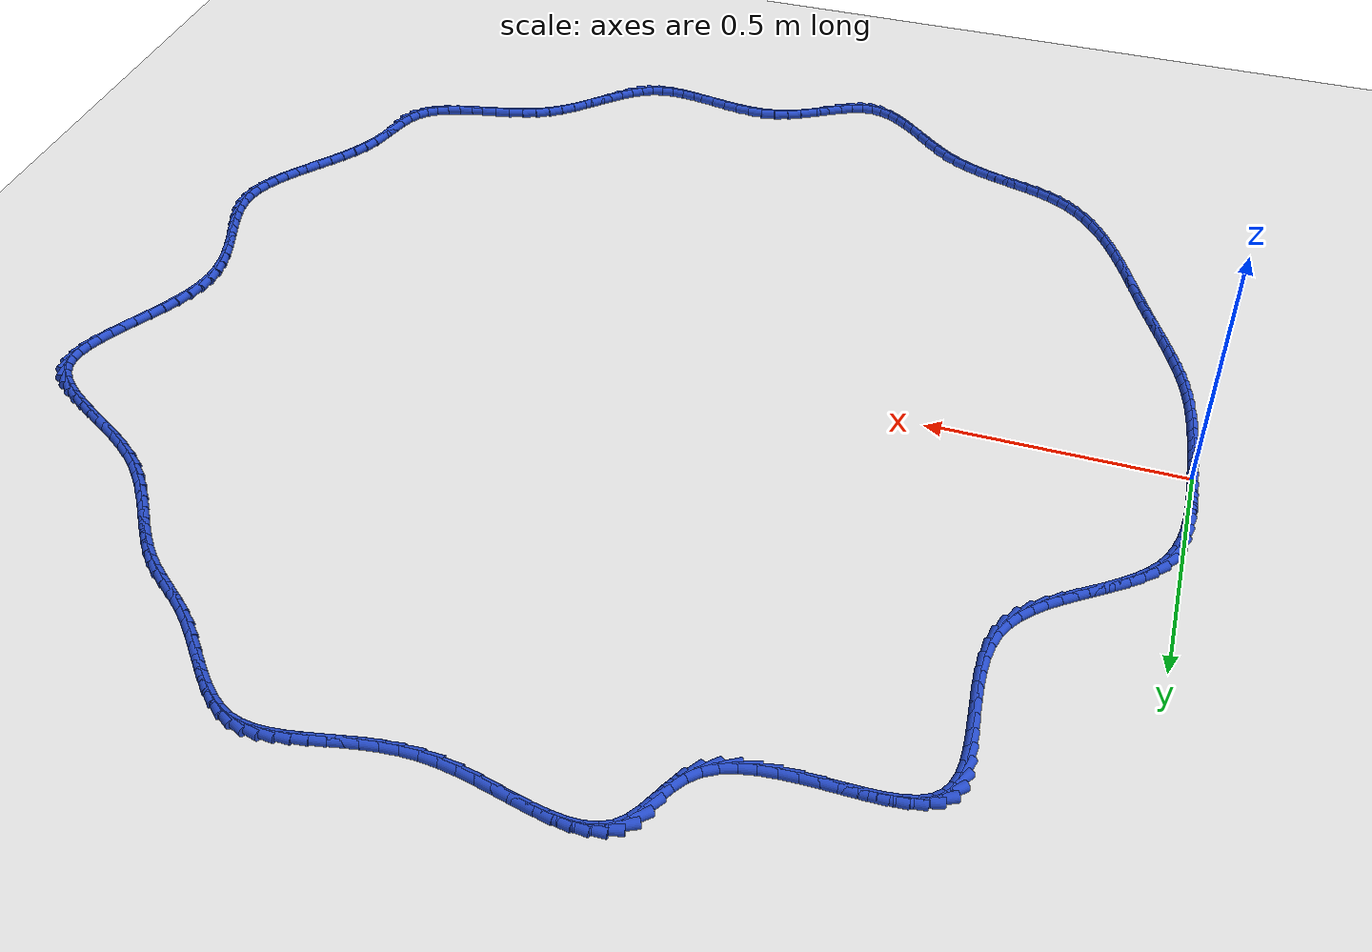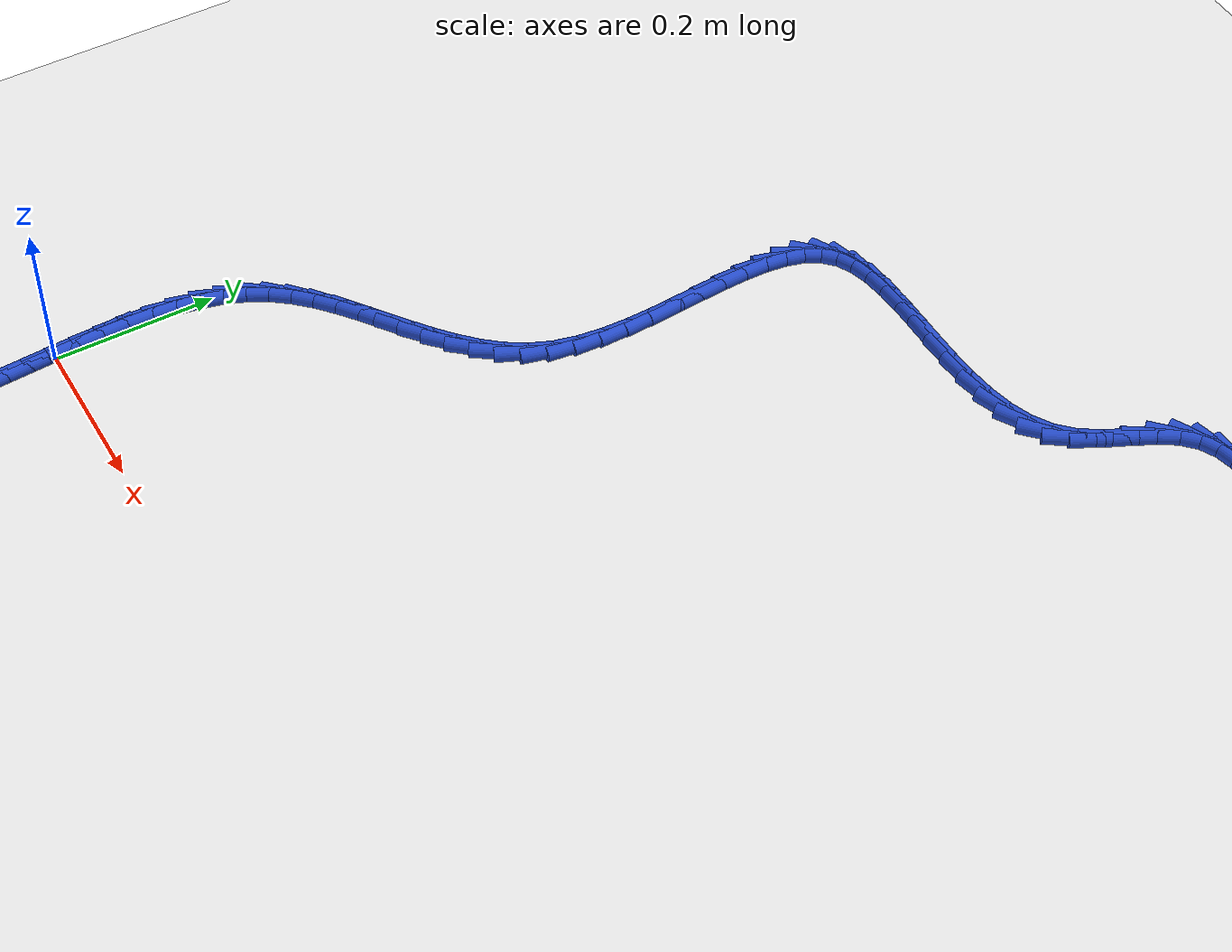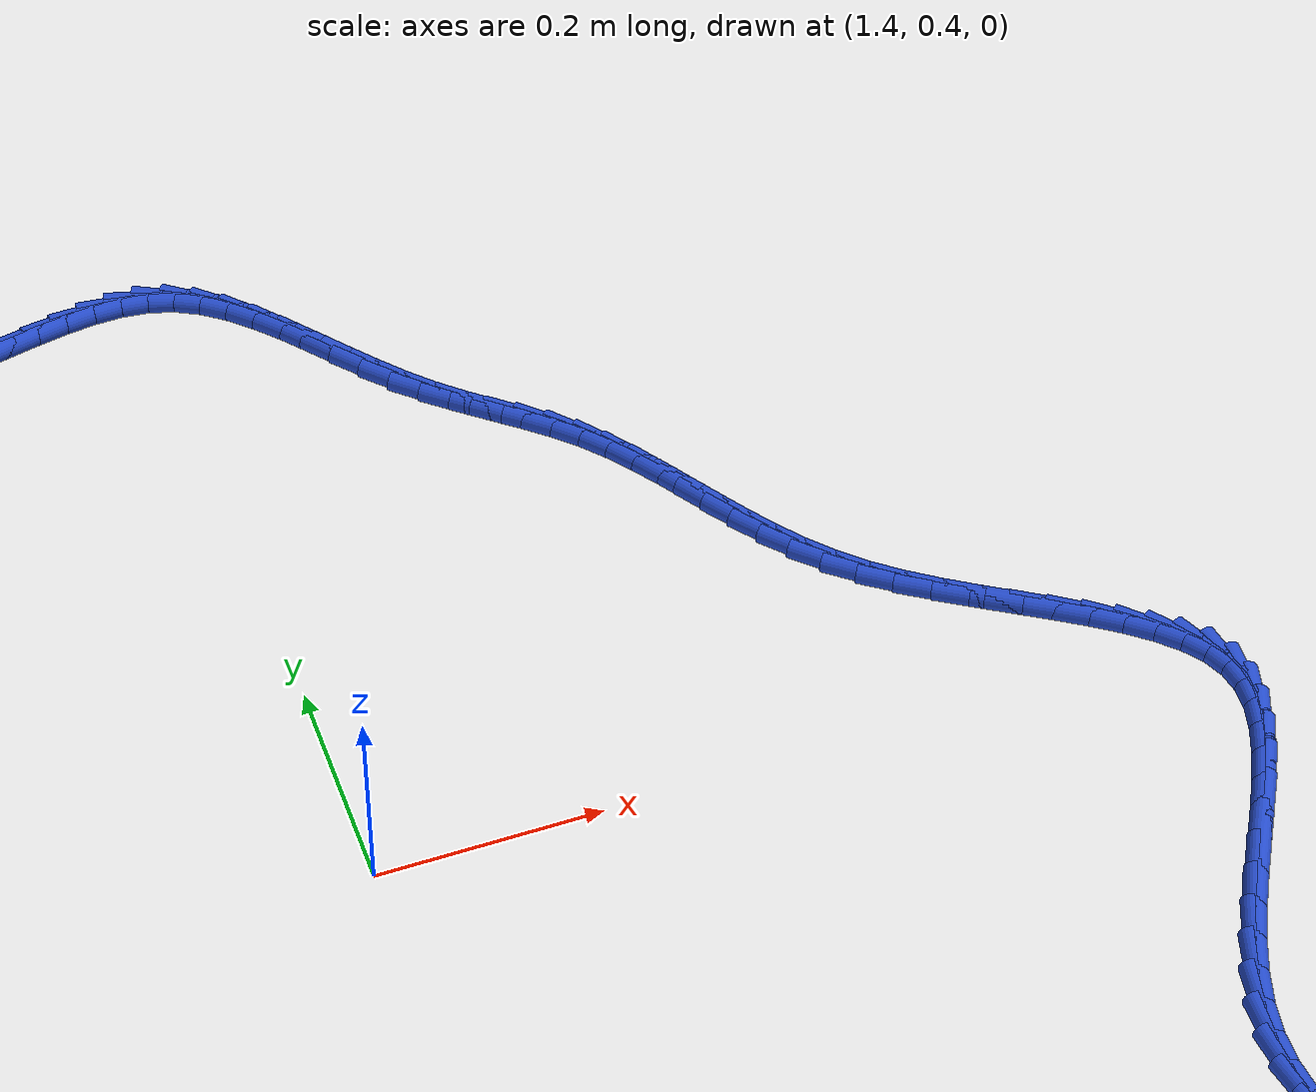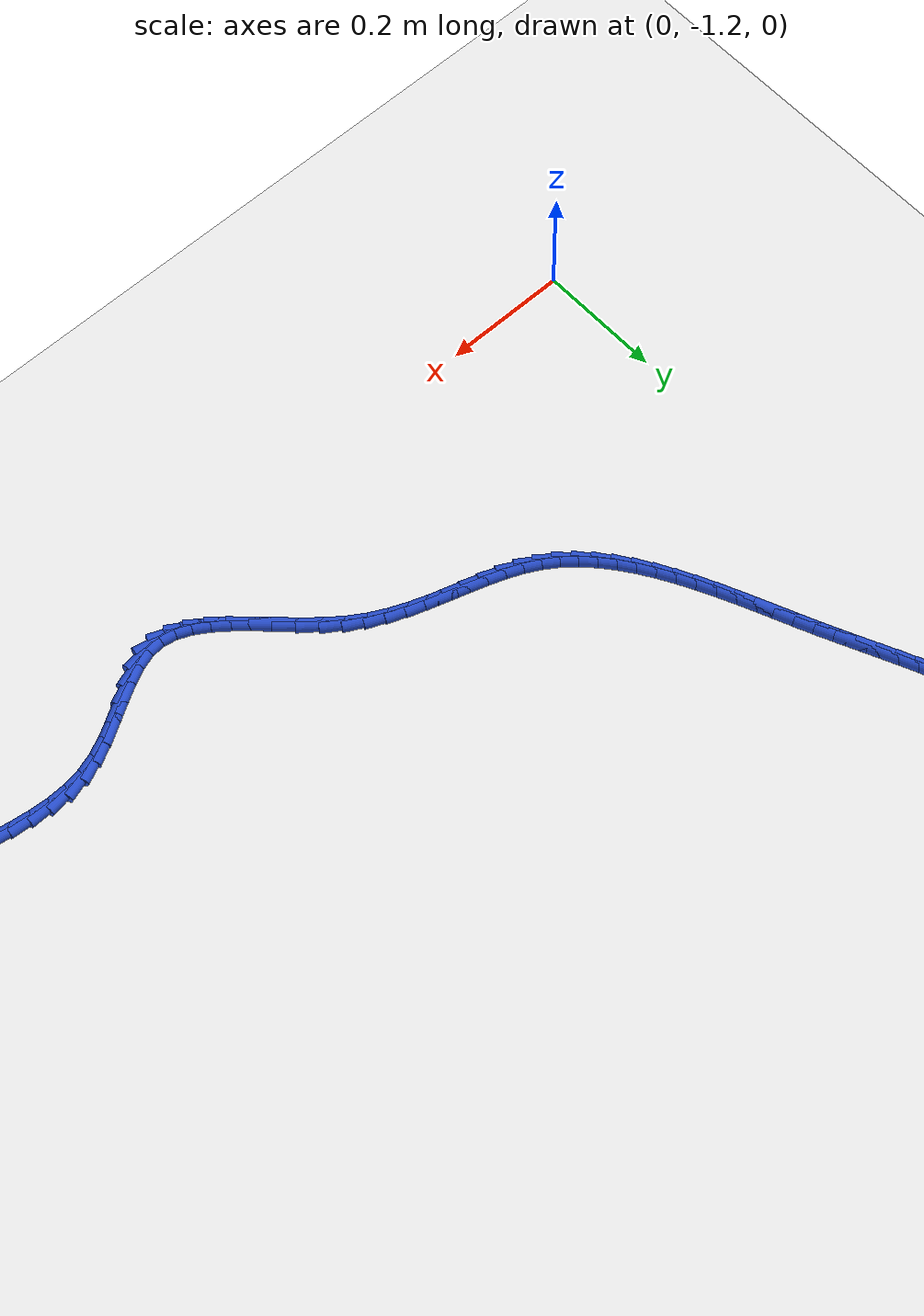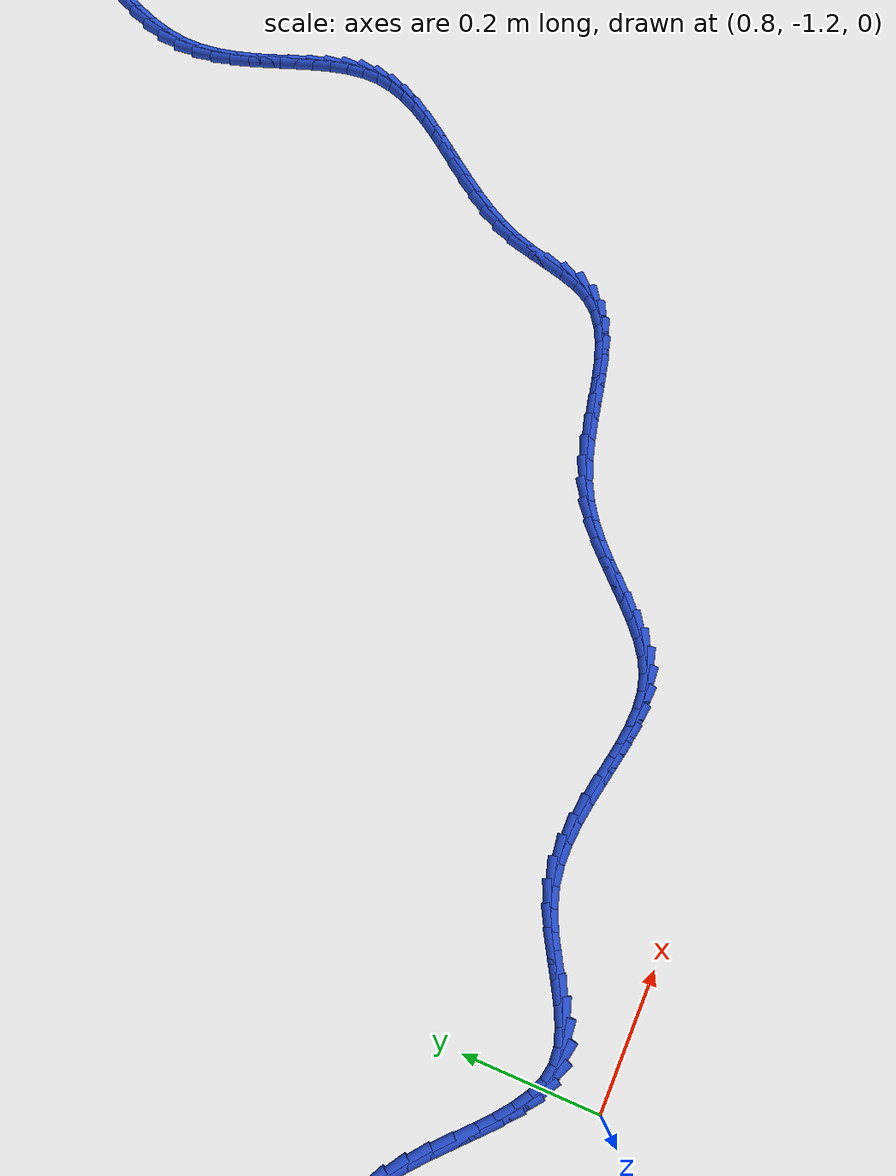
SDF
<sdf version="1.6">
 <world name="default">
  <light name="sun" type="directional">
   <pose>0 0 10 0 -0 0</pose>
   <diffuse>0.8 0.8 0.8 1</diffuse>
   <specular>0.2 0.2 0.2 1</specular>
   <attenuation>
    <range>1000</range>
    <constant>0.9</constant>
    <linear>0.01</linear>
    <quadratic>0.001</quadratic>
   </attenuation>
   <direction>-0.5 0.1 -0.9</direction>
  </light>
  <model name="ground_plane">
   <static>1</static>
   <link name="link">
    <collision name="collision">
     <geometry><plane><normal>0 0 1</normal><size>100 100</size></plane></geometry>
     <surface><friction><ode><mu>100</mu><mu2>50</mu2></ode></friction></surface>
    </collision>
    <visual name="visual">
     <cast_shadows>0</cast_shadows>
     <geometry><plane><normal>0 0 1</normal><size>100 100</size></plane></geometry>
     <material>
      <script><uri>file://media/materials/scripts/gazebo.material</uri><name>Gazebo/WhiteGlow</name></script>
     </material>
    </visual>
   </link>
  </model>
  <gravity>0 0 -9.8</gravity>
  <magnetic_field>6e-06 2.3e-05 -4.2e-05</magnetic_field>
  <atmosphere type="adiabatic"/>
  <physics name="default_physics" default="0" type="ode">
   <max_step_size>0.001</max_step_size>
   <real_time_factor>1</real_time_factor>
   <real_time_update_rate>1000</real_time_update_rate>
  </physics>
  <scene><ambient>0.4 0.4 0.4 1</ambient><background>0.7 0.7 0.7 1</background><shadows>1</shadows></scene>
  <spherical_coordinates>
   <surface_model>EARTH_WGS84</surface_model>
   <latitude_deg>0</latitude_deg>
   <longitude_deg>0</longitude_deg>
   <elevation>0</elevation>
   <heading_deg>0</heading_deg>
  </spherical_coordinates>
  <model name="line">
   <link name="link_0">
    <pose>-1.5178830414797062e-17 -4.163336342344337e-17 0.01 0 1.57 -1.5154828405450358</pose>
    <collision name="collision">
     <geometry><cylinder><radius>0.01</radius><length>0.08</length></cylinder></geometry>
    </collision>
    <visual name="visual">
     <material>
      <script><name>Gazebo/Blue</name><uri>file://media/materials/scripts/gazebo.material</uri></script>
     </material>
     <geometry><cylinder><radius>0.01</radius><length>0.08</length></cylinder></geometry>
    </visual>
   </link>
   <link name="link_1">
    <pose>-0.0017155117721361344 0.030982712327724496 0.01 0 1.57 -1.5299890894671335</pose>
    <collision name="collision">
     <geometry><cylinder><radius>0.01</radius><length>0.08</length></cylinder></geometry>
    </collision>
    <visual name="visual">
     <material>
      <script><name>Gazebo/Blue</name><uri>file://media/materials/scripts/gazebo.material</uri></script>
     </material>
     <geometry><cylinder><radius>0.01</radius><length>0.08</length></cylinder></geometry>
    </visual>
   </link>
   <link name="link_2">
    <pose>-0.0029866828701591882 0.06211604810824366 0.01 0 1.57 -1.5573828331246513</pose>
    <collision name="collision">
     <geometry><cylinder><radius>0.01</radius><length>0.08</length></cylinder></geometry>
    </collision>
    <visual name="visual">
     <material>
      <script><name>Gazebo/Blue</name><uri>file://media/materials/scripts/gazebo.material</uri></script>
     </material>
     <geometry><cylinder><radius>0.01</radius><length>0.08</length></cylinder></geometry>
    </visual>
   </link>
   <link name="link_3">
    <pose>-0.0034025203476769107 0.09311561824485003 0.01 0 1.57 1.5429928417432854</pose>
    <collision name="collision">
     <geometry><cylinder><radius>0.01</radius><length>0.08</length></cylinder></geometry>
    </collision>
    <visual name="visual">
     <material>
      <script><name>Gazebo/Blue</name><uri>file://media/materials/scripts/gazebo.material</uri></script>
     </material>
     <geometry><cylinder><radius>0.01</radius><length>0.08</length></cylinder></geometry>
    </visual>
   </link>
   <link name="link_4">
    <pose>-0.0025520312582970354 0.12369703364083609 0.01 0 1.57 1.4863954331858804</pose>
    <collision name="collision">
     <geometry><cylinder><radius>0.01</radius><length>0.08</length></cylinder></geometry>
    </collision>
    <visual name="visual">
     <material>
      <script><name>Gazebo/Blue</name><uri>file://media/materials/scripts/gazebo.material</uri></script>
     </material>
     <geometry><cylinder><radius>0.01</radius><length>0.08</length></cylinder></geometry>
    </visual>
   </link>
   <link name="link_5">
    <pose>-2.4222655627299805e-05 0.15357590519949446 0.01 0 1.57 1.41236344065607</pose>
    <collision name="collision">
     <geometry><cylinder><radius>0.01</radius><length>0.08</length></cylinder></geometry>
    </collision>
    <visual name="visual">
     <material>
      <script><name>Gazebo/Blue</name><uri>file://media/materials/scripts/gazebo.material</uri></script>
     </material>
     <geometry><cylinder><radius>0.01</radius><length>0.08</length></cylinder></geometry>
    </visual>
   </link>
   <link name="link_6">
    <pose>0.004591898406724573 0.18246784382411768 0.01 0 1.57 1.31866553774087</pose>
    <collision name="collision">
     <geometry><cylinder><radius>0.01</radius><length>0.08</length></cylinder></geometry>
    </collision>
    <visual name="visual">
     <material>
      <script><name>Gazebo/Blue</name><uri>file://media/materials/scripts/gazebo.material</uri></script>
     </material>
     <geometry><cylinder><radius>0.01</radius><length>0.08</length></cylinder></geometry>
    </visual>
   </link>
   <link name="link_7">
    <pose>0.01170732487515084 0.21008846041799822 0.01 0 1.57 1.2035970532807585</pose>
    <collision name="collision">
     <geometry><cylinder><radius>0.01</radius><length>0.08</length></cylinder></geometry>
    </collision>
    <visual name="visual">
     <material>
      <script><name>Gazebo/Blue</name><uri>file://media/materials/scripts/gazebo.material</uri></script>
     </material>
     <geometry><cylinder><radius>0.01</radius><length>0.08</length></cylinder></geometry>
    </visual>
   </link>
   <link name="link_8">
    <pose>0.021733049696043765 0.23615336588442862 0.01 0 1.57 1.0672150120510964</pose>
    <collision name="collision">
     <geometry><cylinder><radius>0.01</radius><length>0.08</length></cylinder></geometry>
    </collision>
    <visual name="visual">
     <material>
      <script><name>Gazebo/Blue</name><uri>file://media/materials/scripts/gazebo.material</uri></script>
     </material>
     <geometry><cylinder><radius>0.01</radius><length>0.08</length></cylinder></geometry>
    </visual>
   </link>
   <link name="link_9">
    <pose>0.03508001064080044 0.26037820624782937 0.01 0 1.57 0.9222931940276594</pose>
    <collision name="collision">
     <geometry><cylinder><radius>0.01</radius><length>0.08</length></cylinder></geometry>
    </collision>
    <visual name="visual">
     <material>
      <script><name>Gazebo/Blue</name><uri>file://media/materials/scripts/gazebo.material</uri></script>
     </material>
     <geometry><cylinder><radius>0.01</radius><length>0.08</length></cylinder></geometry>
    </visual>
   </link>
   <link name="link_10">
    <pose>0.05193623822241579 0.2826205170658451 0.01 0 1.57 0.8041674025619753</pose>
    <collision name="collision">
     <geometry><cylinder><radius>0.01</radius><length>0.08</length></cylinder></geometry>
    </collision>
    <visual name="visual">
     <material>
      <script><name>Gazebo/Blue</name><uri>file://media/materials/scripts/gazebo.material</uri></script>
     </material>
     <geometry><cylinder><radius>0.01</radius><length>0.08</length></cylinder></geometry>
    </visual>
   </link>
   <link name="link_11">
    <pose>0.07175976107626077 0.30320250977258817 0.01 0 1.57 0.7188729163100174</pose>
    <collision name="collision">
     <geometry><cylinder><radius>0.01</radius><length>0.08</length></cylinder></geometry>
    </collision>
    <visual name="visual">
     <material>
      <script><name>Gazebo/Blue</name><uri>file://media/materials/scripts/gazebo.material</uri></script>
     </material>
     <geometry><cylinder><radius>0.01</radius><length>0.08</length></cylinder></geometry>
    </visual>
   </link>
   <link name="link_12">
    <pose>0.09385940275769401 0.3225413709021713 0.01 0 1.57 0.6634476932160228</pose>
    <collision name="collision">
     <geometry><cylinder><radius>0.01</radius><length>0.08</length></cylinder></geometry>
    </collision>
    <visual name="visual">
     <material>
      <script><name>Gazebo/Blue</name><uri>file://media/materials/scripts/gazebo.material</uri></script>
     </material>
     <geometry><cylinder><radius>0.01</radius><length>0.08</length></cylinder></geometry>
    </visual>
   </link>
   <link name="link_13">
    <pose>0.11754398682207418 0.3410542869887078 0.01 0 1.57 0.6348630785416622</pose>
    <collision name="collision">
     <geometry><cylinder><radius>0.01</radius><length>0.08</length></cylinder></geometry>
    </collision>
    <visual name="visual">
     <material>
      <script><name>Gazebo/Blue</name><uri>file://media/materials/scripts/gazebo.material</uri></script>
     </material>
     <geometry><cylinder><radius>0.01</radius><length>0.08</length></cylinder></geometry>
    </visual>
   </link>
   <link name="link_14">
    <pose>0.14212233682475983 0.35915844456631046 0.01 0 1.57 0.6311698076487244</pose>
    <collision name="collision">
     <geometry><cylinder><radius>0.01</radius><length>0.08</length></cylinder></geometry>
    </collision>
    <visual name="visual">
     <material>
      <script><name>Gazebo/Blue</name><uri>file://media/materials/scripts/gazebo.material</uri></script>
     </material>
     <geometry><cylinder><radius>0.01</radius><length>0.08</length></cylinder></geometry>
    </visual>
   </link>
   <link name="link_15">
    <pose>0.16690327632110977 0.37727103016909247 0.01 0 1.57 0.6518508919850909</pose>
    <collision name="collision">
     <geometry><cylinder><radius>0.01</radius><length>0.08</length></cylinder></geometry>
    </collision>
    <visual name="visual">
     <material>
      <script><name>Gazebo/Blue</name><uri>file://media/materials/scripts/gazebo.material</uri></script>
     </material>
     <geometry><cylinder><radius>0.01</radius><length>0.08</length></cylinder></geometry>
    </visual>
   </link>
   <link name="link_16">
    <pose>0.19119562886648253 0.3958092303311668 0.01 0 1.57 0.6978075429111191</pose>
    <collision name="collision">
     <geometry><cylinder><radius>0.01</radius><length>0.08</length></cylinder></geometry>
    </collision>
    <visual name="visual">
     <material>
      <script><name>Gazebo/Blue</name><uri>file://media/materials/scripts/gazebo.material</uri></script>
     </material>
     <geometry><cylinder><radius>0.01</radius><length>0.08</length></cylinder></geometry>
    </visual>
   </link>
   <link name="link_17">
    <pose>0.21430821801623676 0.4151902315866464 0.01 0 1.57 0.7710576328956202</pose>
    <collision name="collision">
     <geometry><cylinder><radius>0.01</radius><length>0.08</length></cylinder></geometry>
    </collision>
    <visual name="visual">
     <material>
      <script><name>Gazebo/Blue</name><uri>file://media/materials/scripts/gazebo.material</uri></script>
     </material>
     <geometry><cylinder><radius>0.01</radius><length>0.08</length></cylinder></geometry>
    </visual>
   </link>
   <link name="link_18">
    <pose>0.23554986732573116 0.4358312204696444 0.01 0 1.57 0.8739182883156523</pose>
    <collision name="collision">
     <geometry><cylinder><radius>0.01</radius><length>0.08</length></cylinder></geometry>
    </collision>
    <visual name="visual">
     <material>
      <script><name>Gazebo/Blue</name><uri>file://media/materials/scripts/gazebo.material</uri></script>
     </material>
     <geometry><cylinder><radius>0.01</radius><length>0.08</length></cylinder></geometry>
    </visual>
   </link>
   <link name="link_19">
    <pose>0.2542294003503243 0.4581493835142735 0.01 0 1.57 1.007251573013523</pose>
    <collision name="collision">
     <geometry><cylinder><radius>0.01</radius><length>0.08</length></cylinder></geometry>
    </collision>
    <visual name="visual">
     <material>
      <script><name>Gazebo/Blue</name><uri>file://media/materials/scripts/gazebo.material</uri></script>
     </material>
     <geometry><cylinder><radius>0.01</radius><length>0.08</length></cylinder></geometry>
    </visual>
   </link>
   <link name="link_20">
    <pose>0.2696556406453749 0.4825619072546472 0.01 0 1.57 1.1674876845816153</pose>
    <collision name="collision">
     <geometry><cylinder><radius>0.01</radius><length>0.08</length></cylinder></geometry>
    </collision>
    <visual name="visual">
     <material>
      <script><name>Gazebo/Blue</name><uri>file://media/materials/scripts/gazebo.material</uri></script>
     </material>
     <geometry><cylinder><radius>0.01</radius><length>0.08</length></cylinder></geometry>
    </visual>
   </link>
   <link name="link_21">
    <pose>0.2811425656276706 0.5094823620049455 0.01 0 1.57 1.3268752912787303</pose>
    <collision name="collision">
     <geometry><cylinder><radius>0.01</radius><length>0.08</length></cylinder></geometry>
    </collision>
    <visual name="visual">
     <material>
      <script><name>Gazebo/Blue</name><uri>file://media/materials/scripts/gazebo.material</uri></script>
     </material>
     <geometry><cylinder><radius>0.01</radius><length>0.08</length></cylinder></geometry>
    </visual>
   </link>
   <link name="link_22">
    <pose>0.28848547787156115 0.5389865950627324 0.01 0 1.57 1.4490515654149474</pose>
    <collision name="collision">
     <geometry><cylinder><radius>0.01</radius><length>0.08</length></cylinder></geometry>
    </collision>
    <visual name="visual">
     <material>
      <script><name>Gazebo/Blue</name><uri>file://media/materials/scripts/gazebo.material</uri></script>
     </material>
     <geometry><cylinder><radius>0.01</radius><length>0.08</length></cylinder></geometry>
    </visual>
   </link>
   <link name="link_23">
    <pose>0.2923463221536812 0.5705423720280268 0.01 0 1.57 1.5365369089055376</pose>
    <collision name="collision">
     <geometry><cylinder><radius>0.01</radius><length>0.08</length></cylinder></geometry>
    </collision>
    <visual name="visual">
     <material>
      <script><name>Gazebo/Blue</name><uri>file://media/materials/scripts/gazebo.material</uri></script>
     </material>
     <geometry><cylinder><radius>0.01</radius><length>0.08</length></cylinder></geometry>
    </visual>
   </link>
   <link name="link_24">
    <pose>0.293477718372949 0.6035538360715009 0.01 0 1.57 -1.545841377254358</pose>
    <collision name="collision">
     <geometry><cylinder><radius>0.01</radius><length>0.08</length></cylinder></geometry>
    </collision>
    <visual name="visual">
     <material>
      <script><name>Gazebo/Blue</name><uri>file://media/materials/scripts/gazebo.material</uri></script>
     </material>
     <geometry><cylinder><radius>0.01</radius><length>0.08</length></cylinder></geometry>
    </visual>
   </link>
   <link name="link_25">
    <pose>0.29263228642828265 0.6374251303638271 0.01 0 1.57 -1.5102399027851348</pose>
    <collision name="collision">
     <geometry><cylinder><radius>0.01</radius><length>0.08</length></cylinder></geometry>
    </collision>
    <visual name="visual">
     <material>
      <script><name>Gazebo/Blue</name><uri>file://media/materials/scripts/gazebo.material</uri></script>
     </material>
     <geometry><cylinder><radius>0.01</radius><length>0.08</length></cylinder></geometry>
    </visual>
   </link>
   <link name="link_26">
    <pose>0.29056264621860056 0.6715603980756771 0.01 0 1.57 -1.4957607199147311</pose>
    <collision name="collision">
     <geometry><cylinder><radius>0.01</radius><length>0.08</length></cylinder></geometry>
    </collision>
    <visual name="visual">
     <material>
      <script><name>Gazebo/Blue</name><uri>file://media/materials/scripts/gazebo.material</uri></script>
     </material>
     <geometry><cylinder><radius>0.01</radius><length>0.08</length></cylinder></geometry>
    </visual>
   </link>
   <link name="link_27">
    <pose>0.28802141764282096 0.7053637823777239 0.01 0 1.57 -1.5021544432532707</pose>
    <collision name="collision">
     <geometry><cylinder><radius>0.01</radius><length>0.08</length></cylinder></geometry>
    </collision>
    <visual name="visual">
     <material>
      <script><name>Gazebo/Blue</name><uri>file://media/materials/scripts/gazebo.material</uri></script>
     </material>
     <geometry><cylinder><radius>0.01</radius><length>0.08</length></cylinder></geometry>
    </visual>
   </link>
   <link name="link_28">
    <pose>0.28576122059986186 0.7382394264406389 0.01 0 1.57 -1.531694559708363</pose>
    <collision name="collision">
     <geometry><cylinder><radius>0.01</radius><length>0.08</length></cylinder></geometry>
    </collision>
    <visual name="visual">
     <material>
      <script><name>Gazebo/Blue</name><uri>file://media/materials/scripts/gazebo.material</uri></script>
     </material>
     <geometry><cylinder><radius>0.01</radius><length>0.08</length></cylinder></geometry>
    </visual>
   </link>
   <link name="link_29">
    <pose>0.28453467498864166 0.7695914734350949 0.01 0 1.57 1.5516513494587065</pose>
    <collision name="collision">
     <geometry><cylinder><radius>0.01</radius><length>0.08</length></cylinder></geometry>
    </collision>
    <visual name="visual">
     <material>
      <script><name>Gazebo/Blue</name><uri>file://media/materials/scripts/gazebo.material</uri></script>
     </material>
     <geometry><cylinder><radius>0.01</radius><length>0.08</length></cylinder></geometry>
    </visual>
   </link>
   <link name="link_30">
    <pose>0.2850944007080785 0.7988240665317639 0.01 0 1.57 1.4544711348709467</pose>
    <collision name="collision">
     <geometry><cylinder><radius>0.01</radius><length>0.08</length></cylinder></geometry>
    </collision>
    <visual name="visual">
     <material>
      <script><name>Gazebo/Blue</name><uri>file://media/materials/scripts/gazebo.material</uri></script>
     </material>
     <geometry><cylinder><radius>0.01</radius><length>0.08</length></cylinder></geometry>
    </visual>
   </link>
   <link name="link_31">
    <pose>0.2881930176570907 0.8253413489013182 0.01 0 1.57 1.3020917603939037</pose>
    <collision name="collision">
     <geometry><cylinder><radius>0.01</radius><length>0.08</length></cylinder></geometry>
    </collision>
    <visual name="visual">
     <material>
      <script><name>Gazebo/Blue</name><uri>file://media/materials/scripts/gazebo.material</uri></script>
     </material>
     <geometry><cylinder><radius>0.01</radius><length>0.08</length></cylinder></geometry>
    </visual>
   </link>
   <link name="link_32">
    <pose>0.29458314573459654 0.8485474637144302 0.01 0 1.57 1.0751516940104155</pose>
    <collision name="collision">
     <geometry><cylinder><radius>0.01</radius><length>0.08</length></cylinder></geometry>
    </collision>
    <visual name="visual">
     <material>
      <script><name>Gazebo/Blue</name><uri>file://media/materials/scripts/gazebo.material</uri></script>
     </material>
     <geometry><cylinder><radius>0.01</radius><length>0.08</length></cylinder></geometry>
    </visual>
   </link>
   <link name="link_33">
    <pose>0.3050174048395141 0.8678465541417721 0.01 0 1.57 0.7715371925944774</pose>
    <collision name="collision">
     <geometry><cylinder><radius>0.01</radius><length>0.08</length></cylinder></geometry>
    </collision>
    <visual name="visual">
     <material>
      <script><name>Gazebo/Blue</name><uri>file://media/materials/scripts/gazebo.material</uri></script>
     </material>
     <geometry><cylinder><radius>0.01</radius><length>0.08</length></cylinder></geometry>
    </visual>
   </link>
   <link name="link_34">
    <pose>0.32023883371235595 0.882651758077651 0.01 0 1.57 0.4701615558088562</pose>
    <collision name="collision">
     <geometry><cylinder><radius>0.01</radius><length>0.08</length></cylinder></geometry>
    </collision>
    <visual name="visual">
     <material>
      <script><name>Gazebo/Blue</name><uri>file://media/materials/scripts/gazebo.material</uri></script>
     </material>
     <geometry><cylinder><radius>0.01</radius><length>0.08</length></cylinder></geometry>
    </visual>
   </link>
   <link name="link_35">
    <pose>0.3404231537281818 0.8929088069400194 0.01 0 1.57 0.2589463208538392</pose>
    <collision name="collision">
     <geometry><cylinder><radius>0.01</radius><length>0.08</length></cylinder></geometry>
    </collision>
    <visual name="visual">
     <material>
      <script><name>Gazebo/Blue</name><uri>file://media/materials/scripts/gazebo.material</uri></script>
     </material>
     <geometry><cylinder><radius>0.01</radius><length>0.08</length></cylinder></geometry>
    </visual>
   </link>
   <link name="link_36">
    <pose>0.36487105955257165 0.8993849010227423 0.01 0 1.57 0.1257769986528519</pose>
    <collision name="collision">
     <geometry><cylinder><radius>0.01</radius><length>0.08</length></cylinder></geometry>
    </collision>
    <visual name="visual">
     <material>
      <script><name>Gazebo/Blue</name><uri>file://media/materials/scripts/gazebo.material</uri></script>
     </material>
     <geometry><cylinder><radius>0.01</radius><length>0.08</length></cylinder></geometry>
    </visual>
   </link>
   <link name="link_37">
    <pose>0.39280847683553327 0.9029174332418181 0.01 0 1.57 0.04649926190605071</pose>
    <collision name="collision">
     <geometry><cylinder><radius>0.01</radius><length>0.08</length></cylinder></geometry>
    </collision>
    <visual name="visual">
     <material>
      <script><name>Gazebo/Blue</name><uri>file://media/materials/scripts/gazebo.material</uri></script>
     </material>
     <geometry><cylinder><radius>0.01</radius><length>0.08</length></cylinder></geometry>
    </visual>
   </link>
   <link name="link_38">
    <pose>0.42346133122707397 0.9043437965132447 0.01 0 1.57 0.004834784378300426</pose>
    <collision name="collision">
     <geometry><cylinder><radius>0.01</radius><length>0.08</length></cylinder></geometry>
    </collision>
    <visual name="visual">
     <material>
      <script><name>Gazebo/Blue</name><uri>file://media/materials/scripts/gazebo.material</uri></script>
     </material>
     <geometry><cylinder><radius>0.01</radius><length>0.08</length></cylinder></geometry>
    </visual>
   </link>
   <link name="link_39">
    <pose>0.45605554837720175 0.9045013837530216 0.01 0 1.57 -0.008109527975908009</pose>
    <collision name="collision">
     <geometry><cylinder><radius>0.01</radius><length>0.08</length></cylinder></geometry>
    </collision>
    <visual name="visual">
     <material>
      <script><name>Gazebo/Blue</name><uri>file://media/materials/scripts/gazebo.material</uri></script>
     </material>
     <geometry><cylinder><radius>0.01</radius><length>0.08</length></cylinder></geometry>
    </visual>
   </link>
   <link name="link_40">
    <pose>0.4898170539359239 0.9042275878771469 0.01 0 1.57 0.0038710100846058213</pose>
    <collision name="collision">
     <geometry><cylinder><radius>0.01</radius><length>0.08</length></cylinder></geometry>
    </collision>
    <visual name="visual">
     <material>
      <script><name>Gazebo/Blue</name><uri>file://media/materials/scripts/gazebo.material</uri></script>
     </material>
     <geometry><cylinder><radius>0.01</radius><length>0.08</length></cylinder></geometry>
    </visual>
   </link>
   <link name="link_41">
    <pose>0.5239717735532485 0.9043598018016192 0.01 0 1.57 0.040707716890212735</pose>
    <collision name="collision">
     <geometry><cylinder><radius>0.01</radius><length>0.08</length></cylinder></geometry>
    </collision>
    <visual name="visual">
     <material>
      <script><name>Gazebo/Blue</name><uri>file://media/materials/scripts/gazebo.material</uri></script>
     </material>
     <geometry><cylinder><radius>0.01</radius><length>0.08</length></cylinder></geometry>
    </visual>
   </link>
   <link name="link_42">
    <pose>0.5577456328791828 0.9057354184424374 0.01 0 1.57 0.1055694596647271</pose>
    <collision name="collision">
     <geometry><cylinder><radius>0.01</radius><length>0.08</length></cylinder></geometry>
    </collision>
    <visual name="visual">
     <material>
      <script><name>Gazebo/Blue</name><uri>file://media/materials/scripts/gazebo.material</uri></script>
     </material>
     <geometry><cylinder><radius>0.01</radius><length>0.08</length></cylinder></geometry>
    </visual>
   </link>
   <link name="link_43">
    <pose>0.5903645575637347 0.9091918307155998 0.01 0 1.57 0.20479786162174354</pose>
    <collision name="collision">
     <geometry><cylinder><radius>0.01</radius><length>0.08</length></cylinder></geometry>
    </collision>
    <visual name="visual">
     <material>
      <script><name>Gazebo/Blue</name><uri>file://media/materials/scripts/gazebo.material</uri></script>
     </material>
     <geometry><cylinder><radius>0.01</radius><length>0.08</length></cylinder></geometry>
    </visual>
   </link>
   <link name="link_44">
    <pose>0.6210544732569114 0.9155664315371048 0.01 0 1.57 0.34729178556325474</pose>
    <collision name="collision">
     <geometry><cylinder><radius>0.01</radius><length>0.08</length></cylinder></geometry>
    </collision>
    <visual name="visual">
     <material>
      <script><name>Gazebo/Blue</name><uri>file://media/materials/scripts/gazebo.material</uri></script>
     </material>
     <geometry><cylinder><radius>0.01</radius><length>0.08</length></cylinder></geometry>
    </visual>
   </link>
   <link name="link_45">
    <pose>0.649041305608721 0.925696613822951 0.01 0 1.57 0.5409398965283047</pose>
    <collision name="collision">
     <geometry><cylinder><radius>0.01</radius><length>0.08</length></cylinder></geometry>
    </collision>
    <visual name="visual">
     <material>
      <script><name>Gazebo/Blue</name><uri>file://media/materials/scripts/gazebo.material</uri></script>
     </material>
     <geometry><cylinder><radius>0.01</radius><length>0.08</length></cylinder></geometry>
    </visual>
   </link>
   <link name="link_46">
    <pose>0.6735509802691708 0.940419770489137 0.01 0 1.57 0.7823945695965688</pose>
    <collision name="collision">
     <geometry><cylinder><radius>0.01</radius><length>0.08</length></cylinder></geometry>
    </collision>
    <visual name="visual">
     <material>
      <script><name>Gazebo/Blue</name><uri>file://media/materials/scripts/gazebo.material</uri></script>
     </material>
     <geometry><cylinder><radius>0.01</radius><length>0.08</length></cylinder></geometry>
    </visual>
   </link>
   <link name="link_47">
    <pose>0.6938162028023086 0.9605636202183369 0.01 0 1.57 1.0023575802286913</pose>
    <collision name="collision">
     <geometry><cylinder><radius>0.01</radius><length>0.08</length></cylinder></geometry>
    </collision>
    <visual name="visual">
     <material>
      <script><name>Gazebo/Blue</name><uri>file://media/materials/scripts/gazebo.material</uri></script>
     </material>
     <geometry><cylinder><radius>0.01</radius><length>0.08</length></cylinder></geometry>
    </visual>
   </link>
   <link name="link_48">
    <pose>0.7099093832979406 0.9857577105278675 0.01 0 1.57 1.1109638539307605</pose>
    <collision name="collision">
     <geometry><cylinder><radius>0.01</radius><length>0.08</length></cylinder></geometry>
    </collision>
    <visual name="visual">
     <material>
      <script><name>Gazebo/Blue</name><uri>file://media/materials/scripts/gazebo.material</uri></script>
     </material>
     <geometry><cylinder><radius>0.01</radius><length>0.08</length></cylinder></geometry>
    </visual>
   </link>
   <link name="link_49">
    <pose>0.7235442671011745 1.0132895739580428 0.01 0 1.57 1.1179962493465696</pose>
    <collision name="collision">
     <geometry><cylinder><radius>0.01</radius><length>0.08</length></cylinder></geometry>
    </collision>
    <visual name="visual">
     <material>
      <script><name>Gazebo/Blue</name><uri>file://media/materials/scripts/gazebo.material</uri></script>
     </material>
     <geometry><cylinder><radius>0.01</radius><length>0.08</length></cylinder></geometry>
    </visual>
   </link>
   <link name="link_50">
    <pose>0.736624652804188 1.04017555680028 0.01 0 1.57 1.0154687004191143</pose>
    <collision name="collision">
     <geometry><cylinder><radius>0.01</radius><length>0.08</length></cylinder></geometry>
    </collision>
    <visual name="visual">
     <material>
      <script><name>Gazebo/Blue</name><uri>file://media/materials/scripts/gazebo.material</uri></script>
     </material>
     <geometry><cylinder><radius>0.01</radius><length>0.08</length></cylinder></geometry>
    </visual>
   </link>
   <link name="link_51">
    <pose>0.7510543389991587 1.063432005345998 0.01 0 1.57 0.7725158500407124</pose>
    <collision name="collision">
     <geometry><cylinder><radius>0.01</radius><length>0.08</length></cylinder></geometry>
    </collision>
    <visual name="visual">
     <material>
      <script><name>Gazebo/Blue</name><uri>file://media/materials/scripts/gazebo.material</uri></script>
     </material>
     <geometry><cylinder><radius>0.01</radius><length>0.08</length></cylinder></geometry>
    </visual>
   </link>
   <link name="link_52">
    <pose>0.768518359638799 1.080451770476029 0.01 0 1.57 0.47516387497505197</pose>
    <collision name="collision">
     <geometry><cylinder><radius>0.01</radius><length>0.08</length></cylinder></geometry>
    </collision>
    <visual name="visual">
     <material>
      <script><name>Gazebo/Blue</name><uri>file://media/materials/scripts/gazebo.material</uri></script>
     </material>
     <geometry><cylinder><radius>0.01</radius><length>0.08</length></cylinder></geometry>
    </visual>
   </link>
   <link name="link_53">
    <pose>0.789253785199944 1.0911197186698152 0.01 0 1.57 0.21692660844581932</pose>
    <collision name="collision">
     <geometry><cylinder><radius>0.01</radius><length>0.08</length></cylinder></geometry>
    </collision>
    <visual name="visual">
     <material>
      <script><name>Gazebo/Blue</name><uri>file://media/materials/scripts/gazebo.material</uri></script>
     </material>
     <geometry><cylinder><radius>0.01</radius><length>0.08</length></cylinder></geometry>
    </visual>
   </link>
   <link name="link_54">
    <pose>0.8129093476070193 1.0963332756835351 0.01 0 1.57 0.025145153268256303</pose>
    <collision name="collision">
     <geometry><cylinder><radius>0.01</radius><length>0.08</length></cylinder></geometry>
    </collision>
    <visual name="visual">
     <material>
      <script><name>Gazebo/Blue</name><uri>file://media/materials/scripts/gazebo.material</uri></script>
     </material>
     <geometry><cylinder><radius>0.01</radius><length>0.08</length></cylinder></geometry>
    </visual>
   </link>
   <link name="link_55">
    <pose>0.8391320809453228 1.0969927893371179 0.01 0 1.57 -0.10490545678973147</pose>
    <collision name="collision">
     <geometry><cylinder><radius>0.01</radius><length>0.08</length></cylinder></geometry>
    </collision>
    <visual name="visual">
     <material>
      <script><name>Gazebo/Blue</name><uri>file://media/materials/scripts/gazebo.material</uri></script>
     </material>
     <geometry><cylinder><radius>0.01</radius><length>0.08</length></cylinder></geometry>
    </visual>
   </link>
   <link name="link_56">
    <pose>0.8675690193001541 1.0939986074504926 0.01 0 1.57 -0.18747127913158096</pose>
    <collision name="collision">
     <geometry><cylinder><radius>0.01</radius><length>0.08</length></cylinder></geometry>
    </collision>
    <visual name="visual">
     <material>
      <script><name>Gazebo/Blue</name><uri>file://media/materials/scripts/gazebo.material</uri></script>
     </material>
     <geometry><cylinder><radius>0.01</radius><length>0.08</length></cylinder></geometry>
    </visual>
   </link>
   <link name="link_57">
    <pose>0.8978671967568109 1.0882510778435888 0.01 0 1.57 -0.23456317669375942</pose>
    <collision name="collision">
     <geometry><cylinder><radius>0.01</radius><length>0.08</length></cylinder></geometry>
    </collision>
    <visual name="visual">
     <material>
      <script><name>Gazebo/Blue</name><uri>file://media/materials/scripts/gazebo.material</uri></script>
     </material>
     <geometry><cylinder><radius>0.01</radius><length>0.08</length></cylinder></geometry>
    </visual>
   </link>
   <link name="link_58">
    <pose>0.9296736474005931 1.0806505483363351 0.01 0 1.57 -0.25388844540533634</pose>
    <collision name="collision">
     <geometry><cylinder><radius>0.01</radius><length>0.08</length></cylinder></geometry>
    </collision>
    <visual name="visual">
     <material>
      <script><name>Gazebo/Blue</name><uri>file://media/materials/scripts/gazebo.material</uri></script>
     </material>
     <geometry><cylinder><radius>0.01</radius><length>0.08</length></cylinder></geometry>
    </visual>
   </link>
   <link name="link_59">
    <pose>0.9626354053167987 1.072097366748661 0.01 0 1.57 -0.24955774497763403</pose>
    <collision name="collision">
     <geometry><cylinder><radius>0.01</radius><length>0.08</length></cylinder></geometry>
    </collision>
    <visual name="visual">
     <material>
      <script><name>Gazebo/Blue</name><uri>file://media/materials/scripts/gazebo.material</uri></script>
     </material>
     <geometry><cylinder><radius>0.01</radius><length>0.08</length></cylinder></geometry>
    </visual>
   </link>
   <link name="link_60">
    <pose>0.9963995045907268 1.063491880900496 0.01 0 1.57 -0.22296661815476587</pose>
    <collision name="collision">
     <geometry><cylinder><radius>0.01</radius><length>0.08</length></cylinder></geometry>
    </collision>
    <visual name="visual">
     <material>
      <script><name>Gazebo/Blue</name><uri>file://media/materials/scripts/gazebo.material</uri></script>
     </material>
     <geometry><cylinder><radius>0.01</radius><length>0.08</length></cylinder></geometry>
    </visual>
   </link>
   <link name="link_61">
    <pose>1.0306129793076757 1.0557344386117689 0.01 0 1.57 -0.17338200599537557</pose>
    <collision name="collision">
     <geometry><cylinder><radius>0.01</radius><length>0.08</length></cylinder></geometry>
    </collision>
    <visual name="visual">
     <material>
      <script><name>Gazebo/Blue</name><uri>file://media/materials/scripts/gazebo.material</uri></script>
     </material>
     <geometry><cylinder><radius>0.01</radius><length>0.08</length></cylinder></geometry>
    </visual>
   </link>
   <link name="link_62">
    <pose>1.0649228635529442 1.0497253877024086 0.01 0 1.57 -0.09835949726790229</pose>
    <collision name="collision">
     <geometry><cylinder><radius>0.01</radius><length>0.08</length></cylinder></geometry>
    </collision>
    <visual name="visual">
     <material>
      <script><name>Gazebo/Blue</name><uri>file://media/materials/scripts/gazebo.material</uri></script>
     </material>
     <geometry><cylinder><radius>0.01</radius><length>0.08</length></cylinder></geometry>
    </visual>
   </link>
   <link name="link_63">
    <pose>1.0989761914190073 1.046365075950536 0.01 0 1.57 -0.00280902387903092</pose>
    <collision name="collision">
     <geometry><cylinder><radius>0.01</radius><length>0.08</length></cylinder></geometry>
    </collision>
    <visual name="visual">
     <material>
      <script><name>Gazebo/Blue</name><uri>file://media/materials/scripts/gazebo.material</uri></script>
     </material>
     <geometry><cylinder><radius>0.01</radius><length>0.08</length></cylinder></geometry>
    </visual>
   </link>
   <link name="link_64">
    <pose>1.1324685399668926 1.0462709948962476 0.01 0 1.57 0.08136396943552691</pose>
    <collision name="collision">
     <geometry><cylinder><radius>0.01</radius><length>0.08</length></cylinder></geometry>
    </collision>
    <visual name="visual">
     <material>
      <script><name>Gazebo/Blue</name><uri>file://media/materials/scripts/gazebo.material</uri></script>
     </material>
     <geometry><cylinder><radius>0.01</radius><length>0.08</length></cylinder></geometry>
    </visual>
   </link>
   <link name="link_65">
    <pose>1.1652865864795063 1.048947109415471 0.01 0 1.57 0.14476173925852065</pose>
    <collision name="collision">
     <geometry><cylinder><radius>0.01</radius><length>0.08</length></cylinder></geometry>
    </collision>
    <visual name="visual">
     <material>
      <script><name>Gazebo/Blue</name><uri>file://media/materials/scripts/gazebo.material</uri></script>
     </material>
     <geometry><cylinder><radius>0.01</radius><length>0.08</length></cylinder></geometry>
    </visual>
   </link>
   <link name="link_66">
    <pose>1.1973640274915764 1.0536234067292674 0.01 0 1.57 0.18668350352479565</pose>
    <collision name="collision">
     <geometry><cylinder><radius>0.01</radius><length>0.08</length></cylinder></geometry>
    </collision>
    <visual name="visual">
     <material>
      <script><name>Gazebo/Blue</name><uri>file://media/materials/scripts/gazebo.material</uri></script>
     </material>
     <geometry><cylinder><radius>0.01</radius><length>0.08</length></cylinder></geometry>
    </visual>
   </link>
   <link name="link_67">
    <pose>1.2286345595378292 1.0595298740586978 0.01 0 1.57 0.20646240324357826</pose>
    <collision name="collision">
     <geometry><cylinder><radius>0.01</radius><length>0.08</length></cylinder></geometry>
    </collision>
    <visual name="visual">
     <material>
      <script><name>Gazebo/Blue</name><uri>file://media/materials/scripts/gazebo.material</uri></script>
     </material>
     <geometry><cylinder><radius>0.01</radius><length>0.08</length></cylinder></geometry>
    </visual>
   </link>
   <link name="link_68">
    <pose>1.2590318791529929 1.0658964986248238 0.01 0 1.57 0.20278229673842127</pose>
    <collision name="collision">
     <geometry><cylinder><radius>0.01</radius><length>0.08</length></cylinder></geometry>
    </collision>
    <visual name="visual">
     <material>
      <script><name>Gazebo/Blue</name><uri>file://media/materials/scripts/gazebo.material</uri></script>
     </material>
     <geometry><cylinder><radius>0.01</radius><length>0.08</length></cylinder></geometry>
    </visual>
   </link>
   <link name="link_69">
    <pose>1.288489682871794 1.0719532676487058 0.01 0 1.57 0.1731707571952304</pose>
    <collision name="collision">
     <geometry><cylinder><radius>0.01</radius><length>0.08</length></cylinder></geometry>
    </collision>
    <visual name="visual">
     <material>
      <script><name>Gazebo/Blue</name><uri>file://media/materials/scripts/gazebo.material</uri></script>
     </material>
     <geometry><cylinder><radius>0.01</radius><length>0.08</length></cylinder></geometry>
    </visual>
   </link>
   <link name="link_70">
    <pose>1.316941667228961 1.0769301683514052 0.01 0 1.57 0.11371602879071308</pose>
    <collision name="collision">
     <geometry><cylinder><radius>0.01</radius><length>0.08</length></cylinder></geometry>
    </collision>
    <visual name="visual">
     <material>
      <script><name>Gazebo/Blue</name><uri>file://media/materials/scripts/gazebo.material</uri></script>
     </material>
     <geometry><cylinder><radius>0.01</radius><length>0.08</length></cylinder></geometry>
    </visual>
   </link>
   <link name="link_71">
    <pose>1.3443215287592207 1.0800571879539838 0.01 0 1.57 0.019322975322153275</pose>
    <collision name="collision">
     <geometry><cylinder><radius>0.01</radius><length>0.08</length></cylinder></geometry>
    </collision>
    <visual name="visual">
     <material>
      <script><name>Gazebo/Blue</name><uri>file://media/materials/scripts/gazebo.material</uri></script>
     </material>
     <geometry><cylinder><radius>0.01</radius><length>0.08</length></cylinder></geometry>
    </visual>
   </link>
   <link name="link_72">
    <pose>1.3705629639973003 1.080564313677502 0.01 0 1.57 -0.11463735208167723</pose>
    <collision name="collision">
     <geometry><cylinder><radius>0.01</radius><length>0.08</length></cylinder></geometry>
    </collision>
    <visual name="visual">
     <material>
      <script><name>Gazebo/Blue</name><uri>file://media/materials/scripts/gazebo.material</uri></script>
     </material>
     <geometry><cylinder><radius>0.01</radius><length>0.08</length></cylinder></geometry>
    </visual>
   </link>
   <link name="link_73">
    <pose>1.3955996694779278 1.0776815327430216 0.01 0 1.57 -0.28809482472202963</pose>
    <collision name="collision">
     <geometry><cylinder><radius>0.01</radius><length>0.08</length></cylinder></geometry>
    </collision>
    <visual name="visual">
     <material>
      <script><name>Gazebo/Blue</name><uri>file://media/materials/scripts/gazebo.material</uri></script>
     </material>
     <geometry><cylinder><radius>0.01</radius><length>0.08</length></cylinder></geometry>
    </visual>
   </link>
   <link name="link_74">
    <pose>1.4193653420786632 1.0706388339651929 0.01 0 1.57 -0.4795923687654513</pose>
    <collision name="collision">
     <geometry><cylinder><radius>0.01</radius><length>0.08</length></cylinder></geometry>
    </collision>
    <visual name="visual">
     <material>
      <script><name>Gazebo/Blue</name><uri>file://media/materials/scripts/gazebo.material</uri></script>
     </material>
     <geometry><cylinder><radius>0.01</radius><length>0.08</length></cylinder></geometry>
    </visual>
   </link>
   <link name="link_75">
    <pose>1.4418532350245061 1.0589430418515193 0.01 0 1.57 -0.6351467838412366</pose>
    <collision name="collision">
     <geometry><cylinder><radius>0.01</radius><length>0.08</length></cylinder></geometry>
    </collision>
    <visual name="visual">
     <material>
      <script><name>Gazebo/Blue</name><uri>file://media/materials/scripts/gazebo.material</uri></script>
     </material>
     <geometry><cylinder><radius>0.01</radius><length>0.08</length></cylinder></geometry>
    </visual>
   </link>
   <link name="link_76">
    <pose>1.4632821403325666 1.0431493525854616 0.01 0 1.57 -0.7463087668512707</pose>
    <collision name="collision">
     <geometry><cylinder><radius>0.01</radius><length>0.08</length></cylinder></geometry>
    </collision>
    <visual name="visual">
     <material>
      <script><name>Gazebo/Blue</name><uri>file://media/materials/scripts/gazebo.material</uri></script>
     </material>
     <geometry><cylinder><radius>0.01</radius><length>0.08</length></cylinder></geometry>
    </visual>
   </link>
   <link name="link_77">
    <pose>1.4839242302619464 1.024061089660365 0.01 0 1.57 -0.8202000287012099</pose>
    <collision name="collision">
     <geometry><cylinder><radius>0.01</radius><length>0.08</length></cylinder></geometry>
    </collision>
    <visual name="visual">
     <material>
      <script><name>Gazebo/Blue</name><uri>file://media/materials/scripts/gazebo.material</uri></script>
     </material>
     <geometry><cylinder><radius>0.01</radius><length>0.08</length></cylinder></geometry>
    </visual>
   </link>
   <link name="link_78">
    <pose>1.5040516770717498 1.002481576569575 0.01 0 1.57 -0.8636223327757733</pose>
    <collision name="collision">
     <geometry><cylinder><radius>0.01</radius><length>0.08</length></cylinder></geometry>
    </collision>
    <visual name="visual">
     <material>
      <script><name>Gazebo/Blue</name><uri>file://media/materials/scripts/gazebo.material</uri></script>
     </material>
     <geometry><cylinder><radius>0.01</radius><length>0.08</length></cylinder></geometry>
    </visual>
   </link>
   <link name="link_79">
    <pose>1.523936653021077 0.9792141368064365 0.01 0 1.57 -0.8812613791826182</pose>
    <collision name="collision">
     <geometry><cylinder><radius>0.01</radius><length>0.08</length></cylinder></geometry>
    </collision>
    <visual name="visual">
     <material>
      <script><name>Gazebo/Blue</name><uri>file://media/materials/scripts/gazebo.material</uri></script>
     </material>
     <geometry><cylinder><radius>0.01</radius><length>0.08</length></cylinder></geometry>
    </visual>
   </link>
   <link name="link_80">
    <pose>1.5438513303690324 0.9550620938642955 0.01 0 1.57 -0.875519704956702</pose>
    <collision name="collision">
     <geometry><cylinder><radius>0.01</radius><length>0.08</length></cylinder></geometry>
    </collision>
    <visual name="visual">
     <material>
      <script><name>Gazebo/Blue</name><uri>file://media/materials/scripts/gazebo.material</uri></script>
     </material>
     <geometry><cylinder><radius>0.01</radius><length>0.08</length></cylinder></geometry>
    </visual>
   </link>
   <link name="link_81">
    <pose>1.5640678813747173 0.930828771236496 0.01 0 1.57 -0.8467334735301223</pose>
    <collision name="collision">
     <geometry><cylinder><radius>0.01</radius><length>0.08</length></cylinder></geometry>
    </collision>
    <visual name="visual">
     <material>
      <script><name>Gazebo/Blue</name><uri>file://media/materials/scripts/gazebo.material</uri></script>
     </material>
     <geometry><cylinder><radius>0.01</radius><length>0.08</length></cylinder></geometry>
    </visual>
   </link>
   <link name="link_82">
    <pose>1.5848584782972348 0.9073174924163846 0.01 0 1.57 -0.7934501923325086</pose>
    <collision name="collision">
     <geometry><cylinder><radius>0.01</radius><length>0.08</length></cylinder></geometry>
    </collision>
    <visual name="visual">
     <material>
      <script><name>Gazebo/Blue</name><uri>file://media/materials/scripts/gazebo.material</uri></script>
     </material>
     <geometry><cylinder><radius>0.01</radius><length>0.08</length></cylinder></geometry>
    </visual>
   </link>
   <link name="link_83">
    <pose>1.6064945206953598 0.885330185959581 0.01 0 1.57 -0.7281467358941833</pose>
    <collision name="collision">
     <geometry><cylinder><radius>0.01</radius><length>0.08</length></cylinder></geometry>
    </collision>
    <visual name="visual">
     <material>
      <script><name>Gazebo/Blue</name><uri>file://media/materials/scripts/gazebo.material</uri></script>
     </material>
     <geometry><cylinder><radius>0.01</radius><length>0.08</length></cylinder></geometry>
    </visual>
   </link>
   <link name="link_84">
    <pose>1.6290157536660645 0.8652505800709968 0.01 0 1.57 -0.6873212385693075</pose>
    <collision name="collision">
     <geometry><cylinder><radius>0.01</radius><length>0.08</length></cylinder></geometry>
    </collision>
    <visual name="visual">
     <material>
      <script><name>Gazebo/Blue</name><uri>file://media/materials/scripts/gazebo.material</uri></script>
     </material>
     <geometry><cylinder><radius>0.01</radius><length>0.08</length></cylinder></geometry>
    </visual>
   </link>
   <link name="link_85">
    <pose>1.651906945276666 0.846460515978572 0.01 0 1.57 -0.6783346617373449</pose>
    <collision name="collision">
     <geometry><cylinder><radius>0.01</radius><length>0.08</length></cylinder></geometry>
    </collision>
    <visual name="visual">
     <material>
      <script><name>Gazebo/Blue</name><uri>file://media/materials/scripts/gazebo.material</uri></script>
     </material>
     <geometry><cylinder><radius>0.01</radius><length>0.08</length></cylinder></geometry>
    </visual>
   </link>
   <link name="link_86">
    <pose>1.6745714836347434 0.8281949215832276 0.01 0 1.57 -0.7029267772788506</pose>
    <collision name="collision">
     <geometry><cylinder><radius>0.01</radius><length>0.08</length></cylinder></geometry>
    </collision>
    <visual name="visual">
     <material>
      <script><name>Gazebo/Blue</name><uri>file://media/materials/scripts/gazebo.material</uri></script>
     </material>
     <geometry><cylinder><radius>0.01</radius><length>0.08</length></cylinder></geometry>
    </visual>
   </link>
   <link name="link_87">
    <pose>1.6964127568478773 0.8096887247858839 0.01 0 1.57 -0.7625897713675887</pose>
    <collision name="collision">
     <geometry><cylinder><radius>0.01</radius><length>0.08</length></cylinder></geometry>
    </collision>
    <visual name="visual">
     <material>
      <script><name>Gazebo/Blue</name><uri>file://media/materials/scripts/gazebo.material</uri></script>
     </material>
     <geometry><cylinder><radius>0.01</radius><length>0.08</length></cylinder></geometry>
    </visual>
   </link>
   <link name="link_88">
    <pose>1.7168348713059405 0.790177581695829 0.01 0 1.57 -0.843900372784086</pose>
    <collision name="collision">
     <geometry><cylinder><radius>0.01</radius><length>0.08</length></cylinder></geometry>
    </collision>
    <visual name="visual">
     <material>
      <script><name>Gazebo/Blue</name><uri>file://media/materials/scripts/gazebo.material</uri></script>
     </material>
     <geometry><cylinder><radius>0.01</radius><length>0.08</length></cylinder></geometry>
    </visual>
   </link>
   <link name="link_89">
    <pose>1.7355146159177919 0.7691735991911116 0.01 0 1.57 -0.910955286009056</pose>
    <collision name="collision">
     <geometry><cylinder><radius>0.01</radius><length>0.08</length></cylinder></geometry>
    </collision>
    <visual name="visual">
     <material>
      <script><name>Gazebo/Blue</name><uri>file://media/materials/scripts/gazebo.material</uri></script>
     </material>
     <geometry><cylinder><radius>0.01</radius><length>0.08</length></cylinder></geometry>
    </visual>
   </link>
   <link name="link_90">
    <pose>1.7528108304997605 0.7468803604439184 0.01 0 1.57 -0.95760517166725</pose>
    <collision name="collision">
     <geometry><cylinder><radius>0.01</radius><length>0.08</length></cylinder></geometry>
    </collision>
    <visual name="visual">
     <material>
      <script><name>Gazebo/Blue</name><uri>file://media/materials/scripts/gazebo.material</uri></script>
     </material>
     <geometry><cylinder><radius>0.01</radius><length>0.08</length></cylinder></geometry>
    </visual>
   </link>
   <link name="link_91">
    <pose>1.7691872550705656 0.7236077984639742 0.01 0 1.57 -0.983978102850983</pose>
    <collision name="collision">
     <geometry><cylinder><radius>0.01</radius><length>0.08</length></cylinder></geometry>
    </collision>
    <visual name="visual">
     <material>
      <script><name>Gazebo/Blue</name><uri>file://media/materials/scripts/gazebo.material</uri></script>
     </material>
     <geometry><cylinder><radius>0.01</radius><length>0.08</length></cylinder></geometry>
    </visual>
   </link>
   <link name="link_92">
    <pose>1.785107629648926 0.6996658462610038 0.01 0 1.57 -0.9906078275194107</pose>
    <collision name="collision">
     <geometry><cylinder><radius>0.01</radius><length>0.08</length></cylinder></geometry>
    </collision>
    <visual name="visual">
     <material>
      <script><name>Gazebo/Blue</name><uri>file://media/materials/scripts/gazebo.material</uri></script>
     </material>
     <geometry><cylinder><radius>0.01</radius><length>0.08</length></cylinder></geometry>
    </visual>
   </link>
   <link name="link_93">
    <pose>1.801035694253562 0.6753644368447325 0.01 0 1.57 -0.9781021345196684</pose>
    <collision name="collision">
     <geometry><cylinder><radius>0.01</radius><length>0.08</length></cylinder></geometry>
    </collision>
    <visual name="visual">
     <material>
      <script><name>Gazebo/Blue</name><uri>file://media/materials/scripts/gazebo.material</uri></script>
     </material>
     <geometry><cylinder><radius>0.01</radius><length>0.08</length></cylinder></geometry>
    </visual>
   </link>
   <link name="link_94">
    <pose>1.8174351889031912 0.6510135032248858 0.01 0 1.57 -0.9470607423933891</pose>
    <collision name="collision">
     <geometry><cylinder><radius>0.01</radius><length>0.08</length></cylinder></geometry>
    </collision>
    <visual name="visual">
     <material>
      <script><name>Gazebo/Blue</name><uri>file://media/materials/scripts/gazebo.material</uri></script>
     </material>
     <geometry><cylinder><radius>0.01</radius><length>0.08</length></cylinder></geometry>
    </visual>
   </link>
   <link name="link_95">
    <pose>1.8347698536165338 0.6269229784111886 0.01 0 1.57 -0.8981997059693798</pose>
    <collision name="collision">
     <geometry><cylinder><radius>0.01</radius><length>0.08</length></cylinder></geometry>
    </collision>
    <visual name="visual">
     <material>
      <script><name>Gazebo/Blue</name><uri>file://media/materials/scripts/gazebo.material</uri></script>
     </material>
     <geometry><cylinder><radius>0.01</radius><length>0.08</length></cylinder></geometry>
    </visual>
   </link>
   <link name="link_96">
    <pose>1.853503428412309 0.6034027954133658 0.01 0 1.57 -0.8326309552382755</pose>
    <collision name="collision">
     <geometry><cylinder><radius>0.01</radius><length>0.08</length></cylinder></geometry>
    </collision>
    <visual name="visual">
     <material>
      <script><name>Gazebo/Blue</name><uri>file://media/materials/scripts/gazebo.material</uri></script>
     </material>
     <geometry><cylinder><radius>0.01</radius><length>0.08</length></cylinder></geometry>
    </visual>
   </link>
   <link name="link_97">
    <pose>1.8740996533092353 0.5807628872411429 0.01 0 1.57 -0.7522805844675242</pose>
    <collision name="collision">
     <geometry><cylinder><radius>0.01</radius><length>0.08</length></cylinder></geometry>
    </collision>
    <visual name="visual">
     <material>
      <script><name>Gazebo/Blue</name><uri>file://media/materials/scripts/gazebo.material</uri></script>
     </material>
     <geometry><cylinder><radius>0.01</radius><length>0.08</length></cylinder></geometry>
    </visual>
   </link>
   <link name="link_98">
    <pose>1.8970202843000696 0.5593122622822257 0.01 0 1.57 -0.67075027537022</pose>
    <collision name="collision">
     <geometry><cylinder><radius>0.01</radius><length>0.08</length></cylinder></geometry>
    </collision>
    <visual name="visual">
     <material>
      <script><name>Gazebo/Blue</name><uri>file://media/materials/scripts/gazebo.material</uri></script>
     </material>
     <geometry><cylinder><radius>0.01</radius><length>0.08</length></cylinder></geometry>
    </visual>
   </link>
   <link name="link_99">
    <pose>1.9223734535218504 0.5391951284581807 0.01 0 1.57 -0.6106774531517228</pose>
    <collision name="collision">
     <geometry><cylinder><radius>0.01</radius><length>0.08</length></cylinder></geometry>
    </collision>
    <visual name="visual">
     <material>
      <script><name>Gazebo/Blue</name><uri>file://media/materials/scripts/gazebo.material</uri></script>
     </material>
     <geometry><cylinder><radius>0.01</radius><length>0.08</length></cylinder></geometry>
    </visual>
   </link>
   <link name="link_100">
    <pose>1.9495089171118882 0.5202022652771817 0.01 0 1.57 -0.5717027698837208</pose>
    <collision name="collision">
     <geometry><cylinder><radius>0.01</radius><length>0.08</length></cylinder></geometry>
    </collision>
    <visual name="visual">
     <material>
      <script><name>Gazebo/Blue</name><uri>file://media/materials/scripts/gazebo.material</uri></script>
     </material>
     <geometry><cylinder><radius>0.01</radius><length>0.08</length></cylinder></geometry>
    </visual>
   </link>
   <link name="link_101">
    <pose>1.9776783996241019 0.5020787662723812 0.01 0 1.57 -0.5516073912957625</pose>
    <collision name="collision">
     <geometry><cylinder><radius>0.01</radius><length>0.08</length></cylinder></geometry>
    </collision>
    <visual name="visual">
     <material>
      <script><name>Gazebo/Blue</name><uri>file://media/materials/scripts/gazebo.material</uri></script>
     </material>
     <geometry><cylinder><radius>0.01</radius><length>0.08</length></cylinder></geometry>
    </visual>
   </link>
   <link name="link_102">
    <pose>2.006133625612408 0.4845697249769307 0.01 0 1.57 -0.5496630083513635</pose>
    <collision name="collision">
     <geometry><cylinder><radius>0.01</radius><length>0.08</length></cylinder></geometry>
    </collision>
    <visual name="visual">
     <material>
      <script><name>Gazebo/Blue</name><uri>file://media/materials/scripts/gazebo.material</uri></script>
     </material>
     <geometry><cylinder><radius>0.01</radius><length>0.08</length></cylinder></geometry>
    </visual>
   </link>
   <link name="link_103">
    <pose>2.0341263196307238 0.4674202349239819 0.01 0 1.57 -0.5667777585296453</pose>
    <collision name="collision">
     <geometry><cylinder><radius>0.01</radius><length>0.08</length></cylinder></geometry>
    </collision>
    <visual name="visual">
     <material>
      <script><name>Gazebo/Blue</name><uri>file://media/materials/scripts/gazebo.material</uri></script>
     </material>
     <geometry><cylinder><radius>0.01</radius><length>0.08</length></cylinder></geometry>
    </visual>
   </link>
   <link name="link_104">
    <pose>2.060908206232969 0.4503753896466866 0.01 0 1.57 -0.6058193651733947</pose>
    <collision name="collision">
     <geometry><cylinder><radius>0.01</radius><length>0.08</length></cylinder></geometry>
    </collision>
    <visual name="visual">
     <material>
      <script><name>Gazebo/Blue</name><uri>file://media/materials/scripts/gazebo.material</uri></script>
     </material>
     <geometry><cylinder><radius>0.01</radius><length>0.08</length></cylinder></geometry>
    </visual>
   </link>
   <link name="link_105">
    <pose>2.08573100997306 0.43318028267819714 0.01 0 1.57 -0.6721969630218647</pose>
    <collision name="collision">
     <geometry><cylinder><radius>0.01</radius><length>0.08</length></cylinder></geometry>
    </collision>
    <visual name="visual">
     <material>
      <script><name>Gazebo/Blue</name><uri>file://media/materials/scripts/gazebo.material</uri></script>
     </material>
     <geometry><cylinder><radius>0.01</radius><length>0.08</length></cylinder></geometry>
    </visual>
   </link>
   <link name="link_106">
    <pose>2.1078464554049154 0.4155800075516651 0.01 0 1.57 -0.7745789707340844</pose>
    <collision name="collision">
     <geometry><cylinder><radius>0.01</radius><length>0.08</length></cylinder></geometry>
    </collision>
    <visual name="visual">
     <material>
      <script><name>Gazebo/Blue</name><uri>file://media/materials/scripts/gazebo.material</uri></script>
     </material>
     <geometry><cylinder><radius>0.01</radius><length>0.08</length></cylinder></geometry>
    </visual>
   </link>
   <link name="link_107">
    <pose>2.1265062670824517 0.3973196578002421 0.01 0 1.57 -0.9248165041522218</pose>
    <collision name="collision">
     <geometry><cylinder><radius>0.01</radius><length>0.08</length></cylinder></geometry>
    </collision>
    <visual name="visual">
     <material>
      <script><name>Gazebo/Blue</name><uri>file://media/materials/scripts/gazebo.material</uri></script>
     </material>
     <geometry><cylinder><radius>0.01</radius><length>0.08</length></cylinder></geometry>
    </visual>
   </link>
   <link name="link_108">
    <pose>2.140962169559588 0.37814432695708006 0.01 0 1.57 -1.133794571797152</pose>
    <collision name="collision">
     <geometry><cylinder><radius>0.01</radius><length>0.08</length></cylinder></geometry>
    </collision>
    <visual name="visual">
     <material>
      <script><name>Gazebo/Blue</name><uri>file://media/materials/scripts/gazebo.material</uri></script>
     </material>
     <geometry><cylinder><radius>0.01</radius><length>0.08</length></cylinder></geometry>
    </visual>
   </link>
   <link name="link_109">
    <pose>2.1504658873902414 0.35779910855533115 0.01 0 1.57 -1.3928247815611445</pose>
    <collision name="collision">
     <geometry><cylinder><radius>0.01</radius><length>0.08</length></cylinder></geometry>
    </collision>
    <visual name="visual">
     <material>
      <script><name>Gazebo/Blue</name><uri>file://media/materials/scripts/gazebo.material</uri></script>
     </material>
     <geometry><cylinder><radius>0.01</radius><length>0.08</length></cylinder></geometry>
    </visual>
   </link>
   <link name="link_110">
    <pose>2.154377081864076 0.33605511130342675 0.01 0 1.57 1.5120159847875245</pose>
    <collision name="collision">
     <geometry><cylinder><radius>0.01</radius><length>0.08</length></cylinder></geometry>
    </collision>
    <visual name="visual">
     <material>
      <script><name>Gazebo/Blue</name><uri>file://media/materials/scripts/gazebo.material</uri></script>
     </material>
     <geometry><cylinder><radius>0.01</radius><length>0.08</length></cylinder></geometry>
    </visual>
   </link>
   <link name="link_111">
    <pose>2.153015317863725 0.3129148022147336 0.01 0 1.57 1.337072285899327</pose>
    <collision name="collision">
     <geometry><cylinder><radius>0.01</radius><length>0.08</length></cylinder></geometry>
    </collision>
    <visual name="visual">
     <material>
      <script><name>Gazebo/Blue</name><uri>file://media/materials/scripts/gazebo.material</uri></script>
     </material>
     <geometry><cylinder><radius>0.01</radius><length>0.08</length></cylinder></geometry>
    </visual>
   </link>
   <link name="link_112">
    <pose>2.1472032148328926 0.2885018957397487 0.01 0 1.57 1.2171761604476727</pose>
    <collision name="collision">
     <geometry><cylinder><radius>0.01</radius><length>0.08</length></cylinder></geometry>
    </collision>
    <visual name="visual">
     <material>
      <script><name>Gazebo/Blue</name><uri>file://media/materials/scripts/gazebo.material</uri></script>
     </material>
     <geometry><cylinder><radius>0.01</radius><length>0.08</length></cylinder></geometry>
    </visual>
   </link>
   <link name="link_113">
    <pose>2.137767819799279 0.2629411734760626 0.01 0 1.57 1.1395609698252003</pose>
    <collision name="collision">
     <geometry><cylinder><radius>0.01</radius><length>0.08</length></cylinder></geometry>
    </collision>
    <visual name="visual">
     <material>
      <script><name>Gazebo/Blue</name><uri>file://media/materials/scripts/gazebo.material</uri></script>
     </material>
     <geometry><cylinder><radius>0.01</radius><length>0.08</length></cylinder></geometry>
    </visual>
   </link>
   <link name="link_114">
    <pose>2.1255361797905863 0.2363574170212649 0.01 0 1.57 1.0938527648775247</pose>
    <collision name="collision">
     <geometry><cylinder><radius>0.01</radius><length>0.08</length></cylinder></geometry>
    </collision>
    <visual name="visual">
     <material>
      <script><name>Gazebo/Blue</name><uri>file://media/materials/scripts/gazebo.material</uri></script>
     </material>
     <geometry><cylinder><radius>0.01</radius><length>0.08</length></cylinder></geometry>
    </visual>
   </link>
   <link name="link_115">
    <pose>2.1113353418345144 0.2088754079729452 0.01 0 1.57 1.0733360823914446</pose>
    <collision name="collision">
     <geometry><cylinder><radius>0.01</radius><length>0.08</length></cylinder></geometry>
    </collision>
    <visual name="visual">
     <material>
      <script><name>Gazebo/Blue</name><uri>file://media/materials/scripts/gazebo.material</uri></script>
     </material>
     <geometry><cylinder><radius>0.01</radius><length>0.08</length></cylinder></geometry>
    </visual>
   </link>
   <link name="link_116">
    <pose>2.095992352958767 0.1806199279286942 0.01 0 1.57 1.0743289666065674</pose>
    <collision name="collision">
     <geometry><cylinder><radius>0.01</radius><length>0.08</length></cylinder></geometry>
    </collision>
    <visual name="visual">
     <material>
      <script><name>Gazebo/Blue</name><uri>file://media/materials/scripts/gazebo.material</uri></script>
     </material>
     <geometry><cylinder><radius>0.01</radius><length>0.08</length></cylinder></geometry>
    </visual>
   </link>
   <link name="link_117">
    <pose>2.080334260191043 0.1517157584861015 0.01 0 1.57 1.0954709363281254</pose>
    <collision name="collision">
     <geometry><cylinder><radius>0.01</radius><length>0.08</length></cylinder></geometry>
    </collision>
    <visual name="visual">
     <material>
      <script><name>Gazebo/Blue</name><uri>file://media/materials/scripts/gazebo.material</uri></script>
     </material>
     <geometry><cylinder><radius>0.01</radius><length>0.08</length></cylinder></geometry>
    </visual>
   </link>
   <link name="link_118">
    <pose>2.0651881105590446 0.12228768124275706 0.01 0 1.57 1.137262635340828</pose>
    <collision name="collision">
     <geometry><cylinder><radius>0.01</radius><length>0.08</length></cylinder></geometry>
    </collision>
    <visual name="visual">
     <material>
      <script><name>Gazebo/Blue</name><uri>file://media/materials/scripts/gazebo.material</uri></script>
     </material>
     <geometry><cylinder><radius>0.01</radius><length>0.08</length></cylinder></geometry>
    </visual>
   </link>
   <link name="link_119">
    <pose>2.051380951090473 0.09246047779625041 0.01 0 1.57 1.201783113498387</pose>
    <collision name="collision">
     <geometry><cylinder><radius>0.01</radius><length>0.08</length></cylinder></geometry>
    </collision>
    <visual name="visual">
     <material>
      <script><name>Gazebo/Blue</name><uri>file://media/materials/scripts/gazebo.material</uri></script>
     </material>
     <geometry><cylinder><radius>0.01</radius><length>0.08</length></cylinder></geometry>
    </visual>
   </link>
   <link name="link_120">
    <pose>2.0397398288130293 0.06235892974417229 0.01 0 1.57 1.2923480377213328</pose>
    <collision name="collision">
     <geometry><cylinder><radius>0.01</radius><length>0.08</length></cylinder></geometry>
    </collision>
    <visual name="visual">
     <material>
      <script><name>Gazebo/Blue</name><uri>file://media/materials/scripts/gazebo.material</uri></script>
     </material>
     <geometry><cylinder><radius>0.01</radius><length>0.08</length></cylinder></geometry>
    </visual>
   </link>
   <link name="link_121">
    <pose>2.031091790754415 0.03210781868411228 0.01 0 1.57 1.412663990231116</pose>
    <collision name="collision">
     <geometry><cylinder><radius>0.01</radius><length>0.08</length></cylinder></geometry>
    </collision>
    <visual name="visual">
     <material>
      <script><name>Gazebo/Blue</name><uri>file://media/materials/scripts/gazebo.material</uri></script>
     </material>
     <geometry><cylinder><radius>0.01</radius><length>0.08</length></cylinder></geometry>
    </visual>
   </link>
   <link name="link_122">
    <pose>2.026263883942331 0.0018319262136603093 0.01 0 1.57 1.5565875524114932</pose>
    <collision name="collision">
     <geometry><cylinder><radius>0.01</radius><length>0.08</length></cylinder></geometry>
    </collision>
    <visual name="visual">
     <material>
      <script><name>Gazebo/Blue</name><uri>file://media/materials/scripts/gazebo.material</uri></script>
     </material>
     <geometry><cylinder><radius>0.01</radius><length>0.08</length></cylinder></geometry>
    </visual>
   </link>
   <link name="link_123">
    <pose>2.025834950785543 -0.02835394901801322 0.01 0 1.57 -1.4571570361159907</pose>
    <collision name="collision">
     <geometry><cylinder><radius>0.01</radius><length>0.08</length></cylinder></geometry>
    </collision>
    <visual name="visual">
     <material>
      <script><name>Gazebo/Blue</name><uri>file://media/materials/scripts/gazebo.material</uri></script>
     </material>
     <geometry><cylinder><radius>0.01</radius><length>0.08</length></cylinder></geometry>
    </visual>
   </link>
   <link name="link_124">
    <pose>2.0292618695340296 -0.05838013447733474 0.01 0 1.57 -1.3585802236031501</pose>
    <collision name="collision">
     <geometry><cylinder><radius>0.01</radius><length>0.08</length></cylinder></geometry>
    </collision>
    <visual name="visual">
     <material>
      <script><name>Gazebo/Blue</name><uri>file://media/materials/scripts/gazebo.material</uri></script>
     </material>
     <geometry><cylinder><radius>0.01</radius><length>0.08</length></cylinder></geometry>
    </visual>
   </link>
   <link name="link_125">
    <pose>2.0356846486567606 -0.08818970233585867 0.01 0 1.57 -1.288751839544415</pose>
    <collision name="collision">
     <geometry><cylinder><radius>0.01</radius><length>0.08</length></cylinder></geometry>
    </collision>
    <visual name="visual">
     <material>
      <script><name>Gazebo/Blue</name><uri>file://media/materials/scripts/gazebo.material</uri></script>
     </material>
     <geometry><cylinder><radius>0.01</radius><length>0.08</length></cylinder></geometry>
    </visual>
   </link>
   <link name="link_126">
    <pose>2.0442432776329764 -0.11772572552891612 0.01 0 1.57 -1.2459893423832824</pose>
    <collision name="collision">
     <geometry><cylinder><radius>0.01</radius><length>0.08</length></cylinder></geometry>
    </collision>
    <visual name="visual">
     <material>
      <script><name>Gazebo/Blue</name><uri>file://media/materials/scripts/gazebo.material</uri></script>
     </material>
     <geometry><cylinder><radius>0.01</radius><length>0.08</length></cylinder></geometry>
    </visual>
   </link>
   <link name="link_127">
    <pose>2.0540777459419175 -0.14693127699184047 0.01 0 1.57 -1.2290624591001136</pose>
    <collision name="collision">
     <geometry><cylinder><radius>0.01</radius><length>0.08</length></cylinder></geometry>
    </collision>
    <visual name="visual">
     <material>
      <script><name>Gazebo/Blue</name><uri>file://media/materials/scripts/gazebo.material</uri></script>
     </material>
     <geometry><cylinder><radius>0.01</radius><length>0.08</length></cylinder></geometry>
    </visual>
   </link>
   <link name="link_128">
    <pose>2.064328043062824 -0.17574942965996443 0.01 0 1.57 -1.238042888915521</pose>
    <collision name="collision">
     <geometry><cylinder><radius>0.01</radius><length>0.08</length></cylinder></geometry>
    </collision>
    <visual name="visual">
     <material>
      <script><name>Gazebo/Blue</name><uri>file://media/materials/scripts/gazebo.material</uri></script>
     </material>
     <geometry><cylinder><radius>0.01</radius><length>0.08</length></cylinder></geometry>
    </visual>
   </link>
   <link name="link_129">
    <pose>2.074134158474937 -0.20412325646862062 0.01 0 1.57 -1.2747328422824256</pose>
    <collision name="collision">
     <geometry><cylinder><radius>0.01</radius><length>0.08</length></cylinder></geometry>
    </collision>
    <visual name="visual">
     <material>
      <script><name>Gazebo/Blue</name><uri>file://media/materials/scripts/gazebo.material</uri></script>
     </material>
     <geometry><cylinder><radius>0.01</radius><length>0.08</length></cylinder></geometry>
    </visual>
   </link>
   <link name="link_130">
    <pose>2.0826360816574967 -0.23199583035314164 0.01 0 1.57 -1.3428021208633203</pose>
    <collision name="collision">
     <geometry><cylinder><radius>0.01</radius><length>0.08</length></cylinder></geometry>
    </collision>
    <visual name="visual">
     <material>
      <script><name>Gazebo/Blue</name><uri>file://media/materials/scripts/gazebo.material</uri></script>
     </material>
     <geometry><cylinder><radius>0.01</radius><length>0.08</length></cylinder></geometry>
    </visual>
   </link>
   <link name="link_131">
    <pose>2.0889738020897437 -0.25931022424886024 0.01 0 1.57 -1.4473229487766002</pose>
    <collision name="collision">
     <geometry><cylinder><radius>0.01</radius><length>0.08</length></cylinder></geometry>
    </collision>
    <visual name="visual">
     <material>
      <script><name>Gazebo/Blue</name><uri>file://media/materials/scripts/gazebo.material</uri></script>
     </material>
     <geometry><cylinder><radius>0.01</radius><length>0.08</length></cylinder></geometry>
    </visual>
   </link>
   <link name="link_132">
    <pose>2.0922873092509184 -0.28600951109110967 0.01 0 1.57 1.548930785760204</pose>
    <collision name="collision">
     <geometry><cylinder><radius>0.01</radius><length>0.08</length></cylinder></geometry>
    </collision>
    <visual name="visual">
     <material>
      <script><name>Gazebo/Blue</name><uri>file://media/materials/scripts/gazebo.material</uri></script>
     </material>
     <geometry><cylinder><radius>0.01</radius><length>0.08</length></cylinder></geometry>
    </visual>
   </link>
   <link name="link_133">
    <pose>2.091718113664573 -0.3120369883618591 0.01 0 1.57 1.3797296908291725</pose>
    <collision name="collision">
     <geometry><cylinder><radius>0.01</radius><length>0.08</length></cylinder></geometry>
    </collision>
    <visual name="visual">
     <material>
      <script><name>Gazebo/Blue</name><uri>file://media/materials/scripts/gazebo.material</uri></script>
     </material>
     <geometry><cylinder><radius>0.01</radius><length>0.08</length></cylinder></geometry>
    </visual>
   </link>
   <link name="link_134">
    <pose>2.086813057970458 -0.3373957913553128 0.01 0 1.57 1.232203331616735</pose>
    <collision name="collision">
     <geometry><cylinder><radius>0.01</radius><length>0.08</length></cylinder></geometry>
    </collision>
    <visual name="visual">
     <material>
      <script><name>Gazebo/Blue</name><uri>file://media/materials/scripts/gazebo.material</uri></script>
     </material>
     <geometry><cylinder><radius>0.01</radius><length>0.08</length></cylinder></geometry>
    </visual>
   </link>
   <link name="link_135">
    <pose>2.078067880792949 -0.3622291376771612 0.01 0 1.57 1.1163967884647503</pose>
    <collision name="collision">
     <geometry><cylinder><radius>0.01</radius><length>0.08</length></cylinder></geometry>
    </collision>
    <visual name="visual">
     <material>
      <script><name>Gazebo/Blue</name><uri>file://media/materials/scripts/gazebo.material</uri></script>
     </material>
     <geometry><cylinder><radius>0.01</radius><length>0.08</length></cylinder></geometry>
    </visual>
   </link>
   <link name="link_136">
    <pose>2.066113912941103 -0.3867002619496668 0.01 0 1.57 1.0313423742957604</pose>
    <collision name="collision">
     <geometry><cylinder><radius>0.01</radius><length>0.08</length></cylinder></geometry>
    </collision>
    <visual name="visual">
     <material>
      <script><name>Gazebo/Blue</name><uri>file://media/materials/scripts/gazebo.material</uri></script>
     </material>
     <geometry><cylinder><radius>0.01</radius><length>0.08</length></cylinder></geometry>
    </visual>
   </link>
   <link name="link_137">
    <pose>2.051582485223975 -0.4109723987950921 0.01 0 1.57 0.9737095184026258</pose>
    <collision name="collision">
     <geometry><cylinder><radius>0.01</radius><length>0.08</length></cylinder></geometry>
    </collision>
    <visual name="visual">
     <material>
      <script><name>Gazebo/Blue</name><uri>file://media/materials/scripts/gazebo.material</uri></script>
     </material>
     <geometry><cylinder><radius>0.01</radius><length>0.08</length></cylinder></geometry>
    </visual>
   </link>
   <link name="link_138">
    <pose>2.035104928450622 -0.43520878283569986 0.01 0 1.57 0.9400383143675316</pose>
    <collision name="collision">
     <geometry><cylinder><radius>0.01</radius><length>0.08</length></cylinder></geometry>
    </collision>
    <visual name="visual">
     <material>
      <script><name>Gazebo/Blue</name><uri>file://media/materials/scripts/gazebo.material</uri></script>
     </material>
     <geometry><cylinder><radius>0.01</radius><length>0.08</length></cylinder></geometry>
    </visual>
   </link>
   <link name="link_139">
    <pose>2.0173125734300994 -0.4595726486937523 0.01 0 1.57 0.9276876795746216</pose>
    <collision name="collision">
     <geometry><cylinder><radius>0.01</radius><length>0.08</length></cylinder></geometry>
    </collision>
    <visual name="visual">
     <material>
      <script><name>Gazebo/Blue</name><uri>file://media/materials/scripts/gazebo.material</uri></script>
     </material>
     <geometry><cylinder><radius>0.01</radius><length>0.08</length></cylinder></geometry>
    </visual>
   </link>
   <link name="link_140">
    <pose>1.998836750971464 -0.48422723099151294 0.01 0 1.57 0.9350746995952076</pose>
    <collision name="collision">
     <geometry><cylinder><radius>0.01</radius><length>0.08</length></cylinder></geometry>
    </collision>
    <visual name="visual">
     <material>
      <script><name>Gazebo/Blue</name><uri>file://media/materials/scripts/gazebo.material</uri></script>
     </material>
     <geometry><cylinder><radius>0.01</radius><length>0.08</length></cylinder></geometry>
    </visual>
   </link>
   <link name="link_141">
    <pose>1.9803087918837716 -0.5093357643512426 0.01 0 1.57 0.9616174661129991</pose>
    <collision name="collision">
     <geometry><cylinder><radius>0.01</radius><length>0.08</length></cylinder></geometry>
    </collision>
    <visual name="visual">
     <material>
      <script><name>Gazebo/Blue</name><uri>file://media/materials/scripts/gazebo.material</uri></script>
     </material>
     <geometry><cylinder><radius>0.01</radius><length>0.08</length></cylinder></geometry>
    </visual>
   </link>
   <link name="link_142">
    <pose>1.9623600269760786 -0.5350614833952047 0.01 0 1.57 1.0075469430716104</pose>
    <collision name="collision">
     <geometry><cylinder><radius>0.01</radius><length>0.08</length></cylinder></geometry>
    </collision>
    <visual name="visual">
     <material>
      <script><name>Gazebo/Blue</name><uri>file://media/materials/scripts/gazebo.material</uri></script>
     </material>
     <geometry><cylinder><radius>0.01</radius><length>0.08</length></cylinder></geometry>
    </visual>
   </link>
   <link name="link_143">
    <pose>1.9456217870574417 -0.5615676227456619 0.01 0 1.57 1.0735924194856676</pose>
    <collision name="collision">
     <geometry><cylinder><radius>0.01</radius><length>0.08</length></cylinder></geometry>
    </collision>
    <visual name="visual">
     <material>
      <script><name>Gazebo/Blue</name><uri>file://media/materials/scripts/gazebo.material</uri></script>
     </material>
     <geometry><cylinder><radius>0.01</radius><length>0.08</length></cylinder></geometry>
    </visual>
   </link>
   <link name="link_144">
    <pose>1.9307254029369152 -0.5890174170248762 0.01 0 1.57 1.1604555459437205</pose>
    <collision name="collision">
     <geometry><cylinder><radius>0.01</radius><length>0.08</length></cylinder></geometry>
    </collision>
    <visual name="visual">
     <material>
      <script><name>Gazebo/Blue</name><uri>file://media/materials/scripts/gazebo.material</uri></script>
     </material>
     <geometry><cylinder><radius>0.01</radius><length>0.08</length></cylinder></geometry>
    </visual>
   </link>
   <link name="link_145">
    <pose>1.9183022054235566 -0.6175741008551107 0.01 0 1.57 1.2619222688862324</pose>
    <collision name="collision">
     <geometry><cylinder><radius>0.01</radius><length>0.08</length></cylinder></geometry>
    </collision>
    <visual name="visual">
     <material>
      <script><name>Gazebo/Blue</name><uri>file://media/materials/scripts/gazebo.material</uri></script>
     </material>
     <geometry><cylinder><radius>0.01</radius><length>0.08</length></cylinder></geometry>
    </visual>
   </link>
   <link name="link_146">
    <pose>1.9088176614021874 -0.6472981559028743 0.01 0 1.57 1.324828326039104</pose>
    <collision name="collision">
     <geometry><cylinder><radius>0.01</radius><length>0.08</length></cylinder></geometry>
    </collision>
    <visual name="visual">
     <material>
      <script><name>Gazebo/Blue</name><uri>file://media/materials/scripts/gazebo.material</uri></script>
     </material>
     <geometry><cylinder><radius>0.01</radius><length>0.08</length></cylinder></geometry>
    </visual>
   </link>
   <link name="link_147">
    <pose>1.901274617219261 -0.6773439681652539 0.01 0 1.57 1.3226670640236446</pose>
    <collision name="collision">
     <geometry><cylinder><radius>0.01</radius><length>0.08</length></cylinder></geometry>
    </collision>
    <visual name="visual">
     <material>
      <script><name>Gazebo/Blue</name><uri>file://media/materials/scripts/gazebo.material</uri></script>
     </material>
     <geometry><cylinder><radius>0.01</radius><length>0.08</length></cylinder></geometry>
    </visual>
   </link>
   <link name="link_148">
    <pose>1.8939146991314708 -0.7063943466248471 0.01 0 1.57 1.2480203772547067</pose>
    <collision name="collision">
     <geometry><cylinder><radius>0.01</radius><length>0.08</length></cylinder></geometry>
    </collision>
    <visual name="visual">
     <material>
      <script><name>Gazebo/Blue</name><uri>file://media/materials/scripts/gazebo.material</uri></script>
     </material>
     <geometry><cylinder><radius>0.01</radius><length>0.08</length></cylinder></geometry>
    </visual>
   </link>
   <link name="link_149">
    <pose>1.8849729957350259 -0.7331280501735445 0.01 0 1.57 1.0818809203704731</pose>
    <collision name="collision">
     <geometry><cylinder><radius>0.01</radius><length>0.08</length></cylinder></geometry>
    </collision>
    <visual name="visual">
     <material>
      <script><name>Gazebo/Blue</name><uri>file://media/materials/scripts/gazebo.material</uri></script>
     </material>
     <geometry><cylinder><radius>0.01</radius><length>0.08</length></cylinder></geometry>
    </visual>
   </link>
   <link name="link_150">
    <pose>1.872685650878479 -0.7562247459262164 0.01 0 1.57 0.837390259455404</pose>
    <collision name="collision">
     <geometry><cylinder><radius>0.01</radius><length>0.08</length></cylinder></geometry>
    </collision>
    <visual name="visual">
     <material>
      <script><name>Gazebo/Blue</name><uri>file://media/materials/scripts/gazebo.material</uri></script>
     </material>
     <geometry><cylinder><radius>0.01</radius><length>0.08</length></cylinder></geometry>
    </visual>
   </link>
   <link name="link_151">
    <pose>1.8558813153719185 -0.7748740533716243 0.01 0 1.57 0.6142586294428259</pose>
    <collision name="collision">
     <geometry><cylinder><radius>0.01</radius><length>0.08</length></cylinder></geometry>
    </collision>
    <visual name="visual">
     <material>
      <script><name>Gazebo/Blue</name><uri>file://media/materials/scripts/gazebo.material</uri></script>
     </material>
     <geometry><cylinder><radius>0.01</radius><length>0.08</length></cylinder></geometry>
    </visual>
   </link>
   <link name="link_152">
    <pose>1.8349672529270007 -0.7896242551854119 0.01 0 1.57 0.4452506866545466</pose>
    <collision name="collision">
     <geometry><cylinder><radius>0.01</radius><length>0.08</length></cylinder></geometry>
    </collision>
    <visual name="visual">
     <material>
      <script><name>Gazebo/Blue</name><uri>file://media/materials/scripts/gazebo.material</uri></script>
     </material>
     <geometry><cylinder><radius>0.01</radius><length>0.08</length></cylinder></geometry>
    </visual>
   </link>
   <link name="link_153">
    <pose>1.810610762202967 -0.8012474380614465 0.01 0 1.57 0.3291749541562293</pose>
    <collision name="collision">
     <geometry><cylinder><radius>0.01</radius><length>0.08</length></cylinder></geometry>
    </collision>
    <visual name="visual">
     <material>
      <script><name>Gazebo/Blue</name><uri>file://media/materials/scripts/gazebo.material</uri></script>
     </material>
     <geometry><cylinder><radius>0.01</radius><length>0.08</length></cylinder></geometry>
    </visual>
   </link>
   <link name="link_154">
    <pose>1.783479141859061 -0.8105156886935954 0.01 0 1.57 0.25702983141219127</pose>
    <collision name="collision">
     <geometry><cylinder><radius>0.01</radius><length>0.08</length></cylinder></geometry>
    </collision>
    <visual name="visual">
     <material>
      <script><name>Gazebo/Blue</name><uri>file://media/materials/scripts/gazebo.material</uri></script>
     </material>
     <geometry><cylinder><radius>0.01</radius><length>0.08</length></cylinder></geometry>
    </visual>
   </link>
   <link name="link_155">
    <pose>1.7542396905545246 -0.8182010937757264 0.01 0 1.57 0.2204347367454198</pose>
    <collision name="collision">
     <geometry><cylinder><radius>0.01</radius><length>0.08</length></cylinder></geometry>
    </collision>
    <visual name="visual">
     <material>
      <script><name>Gazebo/Blue</name><uri>file://media/materials/scripts/gazebo.material</uri></script>
     </material>
     <geometry><cylinder><radius>0.01</radius><length>0.08</length></cylinder></geometry>
    </visual>
   </link>
   <link name="link_156">
    <pose>1.7235597069486033 -0.8250757400017068 0.01 0 1.57 0.21400962419500233</pose>
    <collision name="collision">
     <geometry><cylinder><radius>0.01</radius><length>0.08</length></cylinder></geometry>
    </collision>
    <visual name="visual">
     <material>
      <script><name>Gazebo/Blue</name><uri>file://media/materials/scripts/gazebo.material</uri></script>
     </material>
     <geometry><cylinder><radius>0.01</radius><length>0.08</length></cylinder></geometry>
    </visual>
   </link>
   <link name="link_157">
    <pose>1.692106489700538 -0.8319117140654037 0.01 0 1.57 0.23540092606670313</pose>
    <collision name="collision">
     <geometry><cylinder><radius>0.01</radius><length>0.08</length></cylinder></geometry>
    </collision>
    <visual name="visual">
     <material>
      <script><name>Gazebo/Blue</name><uri>file://media/materials/scripts/gazebo.material</uri></script>
     </material>
     <geometry><cylinder><radius>0.01</radius><length>0.08</length></cylinder></geometry>
    </visual>
   </link>
   <link name="link_158">
    <pose>1.6605473374695718 -0.8394811026606845 0.01 0 1.57 0.2848007526488967</pose>
    <collision name="collision">
     <geometry><cylinder><radius>0.01</radius><length>0.08</length></cylinder></geometry>
    </collision>
    <visual name="visual">
     <material>
      <script><name>Gazebo/Blue</name><uri>file://media/materials/scripts/gazebo.material</uri></script>
     </material>
     <geometry><cylinder><radius>0.01</radius><length>0.08</length></cylinder></geometry>
    </visual>
   </link>
   <link name="link_159">
    <pose>1.6295495489149492 -0.8485559924814177 0.01 0 1.57 0.36432676754444265</pose>
    <collision name="collision">
     <geometry><cylinder><radius>0.01</radius><length>0.08</length></cylinder></geometry>
    </collision>
    <visual name="visual">
     <material>
      <script><name>Gazebo/Blue</name><uri>file://media/materials/scripts/gazebo.material</uri></script>
     </material>
     <geometry><cylinder><radius>0.01</radius><length>0.08</length></cylinder></geometry>
    </visual>
   </link>
   <link name="link_160">
    <pose>1.5997804226959111 -0.8599084702214695 0.01 0 1.57 0.47658942197182647</pose>
    <collision name="collision">
     <geometry><cylinder><radius>0.01</radius><length>0.08</length></cylinder></geometry>
    </collision>
    <visual name="visual">
     <material>
      <script><name>Gazebo/Blue</name><uri>file://media/materials/scripts/gazebo.material</uri></script>
     </material>
     <geometry><cylinder><radius>0.01</radius><length>0.08</length></cylinder></geometry>
    </visual>
   </link>
   <link name="link_161">
    <pose>1.5719015489816948 -0.8743018739629826 0.01 0 1.57 0.6000782211275286</pose>
    <collision name="collision">
     <geometry><cylinder><radius>0.01</radius><length>0.08</length></cylinder></geometry>
    </collision>
    <visual name="visual">
     <material>
      <script><name>Gazebo/Blue</name><uri>file://media/materials/scripts/gazebo.material</uri></script>
     </material>
     <geometry><cylinder><radius>0.01</radius><length>0.08</length></cylinder></geometry>
    </visual>
   </link>
   <link name="link_162">
    <pose>1.5461831429823234 -0.8918997356128829 0.01 0 1.57 0.6960551902035438</pose>
    <collision name="collision">
     <geometry><cylinder><radius>0.01</radius><length>0.08</length></cylinder></geometry>
    </collision>
    <visual name="visual">
     <material>
      <script><name>Gazebo/Blue</name><uri>file://media/materials/scripts/gazebo.material</uri></script>
     </material>
     <geometry><cylinder><radius>0.01</radius><length>0.08</length></cylinder></geometry>
    </visual>
   </link>
   <link name="link_163">
    <pose>1.5222588863596431 -0.9118900603001465 0.01 0 1.57 0.7610241458978654</pose>
    <collision name="collision">
     <geometry><cylinder><radius>0.01</radius><length>0.08</length></cylinder></geometry>
    </collision>
    <visual name="visual">
     <material>
      <script><name>Gazebo/Blue</name><uri>file://media/materials/scripts/gazebo.material</uri></script>
     </material>
     <geometry><cylinder><radius>0.01</radius><length>0.08</length></cylinder></geometry>
    </visual>
   </link>
   <link name="link_164">
    <pose>1.4997040547383311 -0.9333713423127067 0.01 0 1.57 0.7959424958872895</pose>
    <collision name="collision">
     <geometry><cylinder><radius>0.01</radius><length>0.08</length></cylinder></geometry>
    </collision>
    <visual name="visual">
     <material>
      <script><name>Gazebo/Blue</name><uri>file://media/materials/scripts/gazebo.material</uri></script>
     </material>
     <geometry><cylinder><radius>0.01</radius><length>0.08</length></cylinder></geometry>
    </visual>
   </link>
   <link name="link_165">
    <pose>1.4780939237430641 -0.9554420759384944 0.01 0 1.57 0.800998833929001</pose>
    <collision name="collision">
     <geometry><cylinder><radius>0.01</radius><length>0.08</length></cylinder></geometry>
    </collision>
    <visual name="visual">
     <material>
      <script><name>Gazebo/Blue</name><uri>file://media/materials/scripts/gazebo.material</uri></script>
     </material>
     <geometry><cylinder><radius>0.01</radius><length>0.08</length></cylinder></geometry>
    </visual>
   </link>
   <link name="link_166">
    <pose>1.4570037689985196 -0.977200755465442 0.01 0 1.57 0.7745708804798379</pose>
    <collision name="collision">
     <geometry><cylinder><radius>0.01</radius><length>0.08</length></cylinder></geometry>
    </collision>
    <visual name="visual">
     <material>
      <script><name>Gazebo/Blue</name><uri>file://media/materials/scripts/gazebo.material</uri></script>
     </material>
     <geometry><cylinder><radius>0.01</radius><length>0.08</length></cylinder></geometry>
    </visual>
   </link>
   <link name="link_167">
    <pose>1.4360088661293744 -0.9977458751814815 0.01 0 1.57 0.7127213934936995</pose>
    <collision name="collision">
     <geometry><cylinder><radius>0.01</radius><length>0.08</length></cylinder></geometry>
    </collision>
    <visual name="visual">
     <material>
      <script><name>Gazebo/Blue</name><uri>file://media/materials/scripts/gazebo.material</uri></script>
     </material>
     <geometry><cylinder><radius>0.01</radius><length>0.08</length></cylinder></geometry>
    </visual>
   </link>
   <link name="link_168">
    <pose>1.4146844907603071 -1.016175929374545 0.01 0 1.57 0.6094628033240533</pose>
    <collision name="collision">
     <geometry><cylinder><radius>0.01</radius><length>0.08</length></cylinder></geometry>
    </collision>
    <visual name="visual">
     <material>
      <script><name>Gazebo/Blue</name><uri>file://media/materials/scripts/gazebo.material</uri></script>
     </material>
     <geometry><cylinder><radius>0.01</radius><length>0.08</length></cylinder></geometry>
    </visual>
   </link>
   <link name="link_169">
    <pose>1.3926059185159936 -1.031589412332564 0.01 0 1.57 0.45905050871153846</pose>
    <collision name="collision">
     <geometry><cylinder><radius>0.01</radius><length>0.08</length></cylinder></geometry>
    </collision>
    <visual name="visual">
     <material>
      <script><name>Gazebo/Blue</name><uri>file://media/materials/scripts/gazebo.material</uri></script>
     </material>
     <geometry><cylinder><radius>0.01</radius><length>0.08</length></cylinder></geometry>
    </visual>
   </link>
   <link name="link_170">
    <pose>1.369348425021111 -1.0430848183434707 0.01 0 1.57 0.2680133254273836</pose>
    <collision name="collision">
     <geometry><cylinder><radius>0.01</radius><length>0.08</length></cylinder></geometry>
    </collision>
    <visual name="visual">
     <material>
      <script><name>Gazebo/Blue</name><uri>file://media/materials/scripts/gazebo.material</uri></script>
     </material>
     <geometry><cylinder><radius>0.01</radius><length>0.08</length></cylinder></geometry>
    </visual>
   </link>
   <link name="link_171">
    <pose>1.344536799510122 -1.0498985984631444 0.01 0 1.57 0.0942628286378651</pose>
    <collision name="collision">
     <geometry><cylinder><radius>0.01</radius><length>0.08</length></cylinder></geometry>
    </collision>
    <visual name="visual">
     <material>
      <script><name>Gazebo/Blue</name><uri>file://media/materials/scripts/gazebo.material</uri></script>
     </material>
     <geometry><cylinder><radius>0.01</radius><length>0.08</length></cylinder></geometry>
    </visual>
   </link>
   <link name="link_172">
    <pose>1.3181983491196567 -1.0523887149656335 0.01 0 1.57 -0.03363402758428632</pose>
    <collision name="collision">
     <geometry><cylinder><radius>0.01</radius><length>0.08</length></cylinder></geometry>
    </collision>
    <visual name="visual">
     <material>
      <script><name>Gazebo/Blue</name><uri>file://media/materials/scripts/gazebo.material</uri></script>
     </material>
     <geometry><cylinder><radius>0.01</radius><length>0.08</length></cylinder></geometry>
    </visual>
   </link>
   <link name="link_173">
    <pose>1.290556170447707 -1.0514586464265725 0.01 0 1.57 -0.11931075538445785</pose>
    <collision name="collision">
     <geometry><cylinder><radius>0.01</radius><length>0.08</length></cylinder></geometry>
    </collision>
    <visual name="visual">
     <material>
      <script><name>Gazebo/Blue</name><uri>file://media/materials/scripts/gazebo.material</uri></script>
     </material>
     <geometry><cylinder><radius>0.01</radius><length>0.08</length></cylinder></geometry>
    </visual>
   </link>
   <link name="link_174">
    <pose>1.2618346655362451 -1.0480155087009866 0.01 0 1.57 -0.16908338078601834</pose>
    <collision name="collision">
     <geometry><cylinder><radius>0.01</radius><length>0.08</length></cylinder></geometry>
    </collision>
    <visual name="visual">
     <material>
      <script><name>Gazebo/Blue</name><uri>file://media/materials/scripts/gazebo.material</uri></script>
     </material>
     <geometry><cylinder><radius>0.01</radius><length>0.08</length></cylinder></geometry>
    </visual>
   </link>
   <link name="link_175">
    <pose>1.2322582364272436 -1.0429664176438997 0.01 0 1.57 -0.18803696415677998</pose>
    <collision name="collision">
     <geometry><cylinder><radius>0.01</radius><length>0.08</length></cylinder></geometry>
    </collision>
    <visual name="visual">
     <material>
      <script><name>Gazebo/Blue</name><uri>file://media/materials/scripts/gazebo.material</uri></script>
     </material>
     <geometry><cylinder><radius>0.01</radius><length>0.08</length></cylinder></geometry>
    </visual>
   </link>
   <link name="link_176">
    <pose>1.2020512851626752 -1.037218489110336 0.01 0 1.57 -0.17901976851910803</pose>
    <collision name="collision">
     <geometry><cylinder><radius>0.01</radius><length>0.08</length></cylinder></geometry>
    </collision>
    <visual name="visual">
     <material>
      <script><name>Gazebo/Blue</name><uri>file://media/materials/scripts/gazebo.material</uri></script>
     </material>
     <geometry><cylinder><radius>0.01</radius><length>0.08</length></cylinder></geometry>
    </visual>
   </link>
   <link name="link_177">
    <pose>1.1714382137845107 -1.0316788389553195 0.01 0 1.57 -0.1426925622535508</pose>
    <collision name="collision">
     <geometry><cylinder><radius>0.01</radius><length>0.08</length></cylinder></geometry>
    </collision>
    <visual name="visual">
     <material>
      <script><name>Gazebo/Blue</name><uri>file://media/materials/scripts/gazebo.material</uri></script>
     </material>
     <geometry><cylinder><radius>0.01</radius><length>0.08</length></cylinder></geometry>
    </visual>
   </link>
   <link name="link_178">
    <pose>1.140643424334725 -1.0272545830338753 0.01 0 1.57 -0.077941992134923</pose>
    <collision name="collision">
     <geometry><cylinder><radius>0.01</radius><length>0.08</length></cylinder></geometry>
    </collision>
    <visual name="visual">
     <material>
      <script><name>Gazebo/Blue</name><uri>file://media/materials/scripts/gazebo.material</uri></script>
     </material>
     <geometry><cylinder><radius>0.01</radius><length>0.08</length></cylinder></geometry>
    </visual>
   </link>
   <link name="link_179">
    <pose>1.1098913188552897 -1.0248528372010273 0.01 0 1.57 0.017314319250920734</pose>
    <collision name="collision">
     <geometry><cylinder><radius>0.01</radius><length>0.08</length></cylinder></geometry>
    </collision>
    <visual name="visual">
     <material>
      <script><name>Gazebo/Blue</name><uri>file://media/materials/scripts/gazebo.material</uri></script>
     </material>
     <geometry><cylinder><radius>0.01</radius><length>0.08</length></cylinder></geometry>
    </visual>
   </link>
   <link name="link_180">
    <pose>1.0794062993881768 -1.0253807173118 0.01 0 1.57 0.14450447529705002</pose>
    <collision name="collision">
     <geometry><cylinder><radius>0.01</radius><length>0.08</length></cylinder></geometry>
    </collision>
    <visual name="visual">
     <material>
      <script><name>Gazebo/Blue</name><uri>file://media/materials/scripts/gazebo.material</uri></script>
     </material>
     <geometry><cylinder><radius>0.01</radius><length>0.08</length></cylinder></geometry>
    </visual>
   </link>
   <link name="link_181">
    <pose>1.049412767975359 -1.0297453392212172 0.01 0 1.57 0.29770691655304515</pose>
    <collision name="collision">
     <geometry><cylinder><radius>0.01</radius><length>0.08</length></cylinder></geometry>
    </collision>
    <visual name="visual">
     <material>
      <script><name>Gazebo/Blue</name><uri>file://media/materials/scripts/gazebo.material</uri></script>
     </material>
     <geometry><cylinder><radius>0.01</radius><length>0.08</length></cylinder></geometry>
    </visual>
   </link>
   <link name="link_182">
    <pose>1.0201234065485865 -1.038732062772616 0.01 0 1.57 0.42603855463510015</pose>
    <collision name="collision">
     <geometry><cylinder><radius>0.01</radius><length>0.08</length></cylinder></geometry>
    </collision>
    <visual name="visual">
     <material>
      <script><name>Gazebo/Blue</name><uri>file://media/materials/scripts/gazebo.material</uri></script>
     </material>
     <geometry><cylinder><radius>0.01</radius><length>0.08</length></cylinder></geometry>
    </visual>
   </link>
   <link name="link_183">
    <pose>0.9916109154937528 -1.0516720298532216 0.01 0 1.57 0.5029017534004454</pose>
    <collision name="collision">
     <geometry><cylinder><radius>0.01</radius><length>0.08</length></cylinder></geometry>
    </collision>
    <visual name="visual">
     <material>
      <script><name>Gazebo/Blue</name><uri>file://media/materials/scripts/gazebo.material</uri></script>
     </material>
     <geometry><cylinder><radius>0.01</radius><length>0.08</length></cylinder></geometry>
    </visual>
   </link>
   <link name="link_184">
    <pose>0.9638558786397932 -1.066939416556198 0.01 0 1.57 0.5333411153434713</pose>
    <collision name="collision">
     <geometry><cylinder><radius>0.01</radius><length>0.08</length></cylinder></geometry>
    </collision>
    <visual name="visual">
     <material>
      <script><name>Gazebo/Blue</name><uri>file://media/materials/scripts/gazebo.material</uri></script>
     </material>
     <geometry><cylinder><radius>0.01</radius><length>0.08</length></cylinder></geometry>
    </visual>
   </link>
   <link name="link_185">
    <pose>0.9368372613281878 -1.0828915850903966 0.01 0 1.57 0.5181107118379943</pose>
    <collision name="collision">
     <geometry><cylinder><radius>0.01</radius><length>0.08</length></cylinder></geometry>
    </collision>
    <visual name="visual">
     <material>
      <script><name>Gazebo/Blue</name><uri>file://media/materials/scripts/gazebo.material</uri></script>
     </material>
     <geometry><cylinder><radius>0.01</radius><length>0.08</length></cylinder></geometry>
    </visual>
   </link>
   <link name="link_186">
    <pose>0.9105340289004193 -1.0978858976646662 0.01 0 1.57 0.45073802725872214</pose>
    <collision name="collision">
     <geometry><cylinder><radius>0.01</radius><length>0.08</length></cylinder></geometry>
    </collision>
    <visual name="visual">
     <material>
      <script><name>Gazebo/Blue</name><uri>file://media/materials/scripts/gazebo.material</uri></script>
     </material>
     <geometry><cylinder><radius>0.01</radius><length>0.08</length></cylinder></geometry>
    </visual>
   </link>
   <link name="link_187">
    <pose>0.8849251466979678 -1.1102797164878584 0.01 0 1.57 0.31592226912365007</pose>
    <collision name="collision">
     <geometry><cylinder><radius>0.01</radius><length>0.08</length></cylinder></geometry>
    </collision>
    <visual name="visual">
     <material>
      <script><name>Gazebo/Blue</name><uri>file://media/materials/scripts/gazebo.material</uri></script>
     </material>
     <geometry><cylinder><radius>0.01</radius><length>0.08</length></cylinder></geometry>
    </visual>
   </link>
   <link name="link_188">
    <pose>0.8599895800623146 -1.1184304037688242 0.01 0 1.57 0.09328224552289062</pose>
    <collision name="collision">
     <geometry><cylinder><radius>0.01</radius><length>0.08</length></cylinder></geometry>
    </collision>
    <visual name="visual">
     <material>
      <script><name>Gazebo/Blue</name><uri>file://media/materials/scripts/gazebo.material</uri></script>
     </material>
     <geometry><cylinder><radius>0.01</radius><length>0.08</length></cylinder></geometry>
    </visual>
   </link>
   <link name="link_189">
    <pose>0.8357058922182701 -1.1207022340284967 0.01 0 1.57 -0.18301170579196788</pose>
    <collision name="collision">
     <geometry><cylinder><radius>0.01</radius><length>0.08</length></cylinder></geometry>
    </collision>
    <visual name="visual">
     <material>
      <script><name>Gazebo/Blue</name><uri>file://media/materials/scripts/gazebo.material</uri></script>
     </material>
     <geometry><cylinder><radius>0.01</radius><length>0.08</length></cylinder></geometry>
    </visual>
   </link>
   <link name="link_190">
    <pose>0.8120028650283561 -1.1163152143100261 0.01 0 1.57 -0.411099257064355</pose>
    <collision name="collision">
     <geometry><cylinder><radius>0.01</radius><length>0.08</length></cylinder></geometry>
    </collision>
    <visual name="visual">
     <material>
      <script><name>Gazebo/Blue</name><uri>file://media/materials/scripts/gazebo.material</uri></script>
     </material>
     <geometry><cylinder><radius>0.01</radius><length>0.08</length></cylinder></geometry>
    </visual>
   </link>
   <link name="link_191">
    <pose>0.7887119863415742 -1.1061618179723955 0.01 0 1.57 -0.5716548274579738</pose>
    <collision name="collision">
     <geometry><cylinder><radius>0.01</radius><length>0.08</length></cylinder></geometry>
    </collision>
    <visual name="visual">
     <material>
      <script><name>Gazebo/Blue</name><uri>file://media/materials/scripts/gazebo.material</uri></script>
     </material>
     <geometry><cylinder><radius>0.01</radius><length>0.08</length></cylinder></geometry>
    </visual>
   </link>
   <link name="link_192">
    <pose>0.7656534797698585 -1.091328148551681 0.01 0 1.57 -0.6753531647949892</pose>
    <collision name="collision">
     <geometry><cylinder><radius>0.01</radius><length>0.08</length></cylinder></geometry>
    </collision>
    <visual name="visual">
     <material>
      <script><name>Gazebo/Blue</name><uri>file://media/materials/scripts/gazebo.material</uri></script>
     </material>
     <geometry><cylinder><radius>0.01</radius><length>0.08</length></cylinder></geometry>
    </visual>
   </link>
   <link name="link_193">
    <pose>0.7426475689251445 -1.0729003095839598 0.01 0 1.57 -0.7355815390486673</pose>
    <collision name="collision">
     <geometry><cylinder><radius>0.01</radius><length>0.08</length></cylinder></geometry>
    </collision>
    <visual name="visual">
     <material>
      <script><name>Gazebo/Blue</name><uri>file://media/materials/scripts/gazebo.material</uri></script>
     </material>
     <geometry><cylinder><radius>0.01</radius><length>0.08</length></cylinder></geometry>
    </visual>
   </link>
   <link name="link_194">
    <pose>0.7195144774193662 -1.051964404605308 0.01 0 1.57 -0.761773076268712</pose>
    <collision name="collision">
     <geometry><cylinder><radius>0.01</radius><length>0.08</length></cylinder></geometry>
    </collision>
    <visual name="visual">
     <material>
      <script><name>Gazebo/Blue</name><uri>file://media/materials/scripts/gazebo.material</uri></script>
     </material>
     <geometry><cylinder><radius>0.01</radius><length>0.08</length></cylinder></geometry>
    </visual>
   </link>
   <link name="link_195">
    <pose>0.6960744288644585 -1.0296065371518028 0.01 0 1.57 -0.7589555474741261</pose>
    <collision name="collision">
     <geometry><cylinder><radius>0.01</radius><length>0.08</length></cylinder></geometry>
    </collision>
    <visual name="visual">
     <material>
      <script><name>Gazebo/Blue</name><uri>file://media/materials/scripts/gazebo.material</uri></script>
     </material>
     <geometry><cylinder><radius>0.01</radius><length>0.08</length></cylinder></geometry>
    </visual>
   </link>
   <link name="link_196">
    <pose>0.6721476468723557 -1.0069128107595204 0.01 0 1.57 -0.728519448872654</pose>
    <collision name="collision">
     <geometry><cylinder><radius>0.01</radius><length>0.08</length></cylinder></geometry>
    </collision>
    <visual name="visual">
     <material>
      <script><name>Gazebo/Blue</name><uri>file://media/materials/scripts/gazebo.material</uri></script>
     </material>
     <geometry><cylinder><radius>0.01</radius><length>0.08</length></cylinder></geometry>
    </visual>
   </link>
   <link name="link_197">
    <pose>0.6475543550549926 -0.9849693289645374 0.01 0 1.57 -0.6688523387672435</pose>
    <collision name="collision">
     <geometry><cylinder><radius>0.01</radius><length>0.08</length></cylinder></geometry>
    </collision>
    <visual name="visual">
     <material>
      <script><name>Gazebo/Blue</name><uri>file://media/materials/scripts/gazebo.material</uri></script>
     </material>
     <geometry><cylinder><radius>0.01</radius><length>0.08</length></cylinder></geometry>
    </visual>
   </link>
   <link name="link_198">
    <pose>0.6221147770243035 -0.9648621953029302 0.01 0 1.57 -0.5781386690121575</pose>
    <collision name="collision">
     <geometry><cylinder><radius>0.01</radius><length>0.08</length></cylinder></geometry>
    </collision>
    <visual name="visual">
     <material>
      <script><name>Gazebo/Blue</name><uri>file://media/materials/scripts/gazebo.material</uri></script>
     </material>
     <geometry><cylinder><radius>0.01</radius><length>0.08</length></cylinder></geometry>
    </visual>
   </link>
   <link name="link_199">
    <pose>0.5956691136410265 -0.9476060988181564 0.01 0 1.57 -0.4828092701590742</pose>
    <collision name="collision">
     <geometry><cylinder><radius>0.01</radius><length>0.08</length></cylinder></geometry>
    </collision>
    <visual name="visual">
     <material>
      <script><name>Gazebo/Blue</name><uri>file://media/materials/scripts/gazebo.material</uri></script>
     </material>
     <geometry><cylinder><radius>0.01</radius><length>0.08</length></cylinder></geometry>
    </visual>
   </link>
   <link name="link_200">
    <pose>0.5683218359665394 -0.9332710177739608 0.01 0 1.57 -0.4058293384883436</pose>
    <collision name="collision">
     <geometry><cylinder><radius>0.01</radius><length>0.08</length></cylinder></geometry>
    </collision>
    <visual name="visual">
     <material>
      <script><name>Gazebo/Blue</name><uri>file://media/materials/scripts/gazebo.material</uri></script>
     </material>
     <geometry><cylinder><radius>0.01</radius><length>0.08</length></cylinder></geometry>
    </visual>
   </link>
   <link name="link_201">
    <pose>0.5403644692302548 -0.9212582508459205 0.01 0 1.57 -0.34947585747080984</pose>
    <collision name="collision">
     <geometry><cylinder><radius>0.01</radius><length>0.08</length></cylinder></geometry>
    </collision>
    <visual name="visual">
     <material>
      <script><name>Gazebo/Blue</name><uri>file://media/materials/scripts/gazebo.material</uri></script>
     </material>
     <geometry><cylinder><radius>0.01</radius><length>0.08</length></cylinder></geometry>
    </visual>
   </link>
   <link name="link_202">
    <pose>0.5120924922423902 -0.9109549634838546 0.01 0 1.57 -0.31461651703703536</pose>
    <collision name="collision">
     <geometry><cylinder><radius>0.01</radius><length>0.08</length></cylinder></geometry>
    </collision>
    <visual name="visual">
     <material>
      <script><name>Gazebo/Blue</name><uri>file://media/materials/scripts/gazebo.material</uri></script>
     </material>
     <geometry><cylinder><radius>0.01</radius><length>0.08</length></cylinder></geometry>
    </visual>
   </link>
   <link name="link_203">
    <pose>0.48380138381316334 -0.9017483211375816 0.01 0 1.57 -0.3018510274024102</pose>
    <collision name="collision">
     <geometry><cylinder><radius>0.01</radius><length>0.08</length></cylinder></geometry>
    </collision>
    <visual name="visual">
     <material>
      <script><name>Gazebo/Blue</name><uri>file://media/materials/scripts/gazebo.material</uri></script>
     </material>
     <geometry><cylinder><radius>0.01</radius><length>0.08</length></cylinder></geometry>
    </visual>
   </link>
   <link name="link_204">
    <pose>0.4557866227527924 -0.8930254892569202 0.01 0 1.57 -0.3120188967539483</pose>
    <collision name="collision">
     <geometry><cylinder><radius>0.01</radius><length>0.08</length></cylinder></geometry>
    </collision>
    <visual name="visual">
     <material>
      <script><name>Gazebo/Blue</name><uri>file://media/materials/scripts/gazebo.material</uri></script>
     </material>
     <geometry><cylinder><radius>0.01</radius><length>0.08</length></cylinder></geometry>
    </visual>
   </link>
   <link name="link_205">
    <pose>0.4283436878714954 -0.8841736332916891 0.01 0 1.57 -0.34643764485766204</pose>
    <collision name="collision">
     <geometry><cylinder><radius>0.01</radius><length>0.08</length></cylinder></geometry>
    </collision>
    <visual name="visual">
     <material>
      <script><name>Gazebo/Blue</name><uri>file://media/materials/scripts/gazebo.material</uri></script>
     </material>
     <geometry><cylinder><radius>0.01</radius><length>0.08</length></cylinder></geometry>
    </visual>
   </link>
   <link name="link_206">
    <pose>0.40176805797949044 -0.8745799186917071 0.01 0 1.57 -0.40679140171701117</pose>
    <collision name="collision">
     <geometry><cylinder><radius>0.01</radius><length>0.08</length></cylinder></geometry>
    </collision>
    <visual name="visual">
     <material>
      <script><name>Gazebo/Blue</name><uri>file://media/materials/scripts/gazebo.material</uri></script>
     </material>
     <geometry><cylinder><radius>0.01</radius><length>0.08</length></cylinder></geometry>
    </visual>
   </link>
   <link name="link_207">
    <pose>0.37635521188699533 -0.8636315109067929 0.01 0 1.57 -0.49450140775604906</pose>
    <collision name="collision">
     <geometry><cylinder><radius>0.01</radius><length>0.08</length></cylinder></geometry>
    </collision>
    <visual name="visual">
     <material>
      <script><name>Gazebo/Blue</name><uri>file://media/materials/scripts/gazebo.material</uri></script>
     </material>
     <geometry><cylinder><radius>0.01</radius><length>0.08</length></cylinder></geometry>
    </visual>
   </link>
   <link name="link_208">
    <pose>0.3524006270918353 -0.850715577904513 0.01 0 1.57 -0.6031734528766335</pose>
    <collision name="collision">
     <geometry><cylinder><radius>0.01</radius><length>0.08</length></cylinder></geometry>
    </collision>
    <visual name="visual">
     <material>
      <script><name>Gazebo/Blue</name><uri>file://media/materials/scripts/gazebo.material</uri></script>
     </material>
     <geometry><cylinder><radius>0.01</radius><length>0.08</length></cylinder></geometry>
    </visual>
   </link>
   <link name="link_209">
    <pose>0.33012145310014235 -0.8353695552791395 0.01 0 1.57 -0.7075279267049432</pose>
    <collision name="collision">
     <geometry><cylinder><radius>0.01</radius><length>0.08</length></cylinder></geometry>
    </collision>
    <visual name="visual">
     <material>
      <script><name>Gazebo/Blue</name><uri>file://media/materials/scripts/gazebo.material</uri></script>
     </material>
     <geometry><cylinder><radius>0.01</radius><length>0.08</length></cylinder></geometry>
    </visual>
   </link>
   <link name="link_210">
    <pose>0.30944524500797704 -0.8176864483997706 0.01 0 1.57 -0.8004239297257473</pose>
    <collision name="collision">
     <geometry><cylinder><radius>0.01</radius><length>0.08</length></cylinder></geometry>
    </collision>
    <visual name="visual">
     <material>
      <script><name>Gazebo/Blue</name><uri>file://media/materials/scripts/gazebo.material</uri></script>
     </material>
     <geometry><cylinder><radius>0.01</radius><length>0.08</length></cylinder></geometry>
    </visual>
   </link>
   <link name="link_211">
    <pose>0.290232646126426 -0.7978876289437594 0.01 0 1.57 -0.8812297714677071</pose>
    <collision name="collision">
     <geometry><cylinder><radius>0.01</radius><length>0.08</length></cylinder></geometry>
    </collision>
    <visual name="visual">
     <material>
      <script><name>Gazebo/Blue</name><uri>file://media/materials/scripts/gazebo.material</uri></script>
     </material>
     <geometry><cylinder><radius>0.01</radius><length>0.08</length></cylinder></geometry>
    </visual>
   </link>
   <link name="link_212">
    <pose>0.2723442997665761 -0.7761944685884596 0.01 0 1.57 -0.9501683976423911</pose>
    <collision name="collision">
     <geometry><cylinder><radius>0.01</radius><length>0.08</length></cylinder></geometry>
    </collision>
    <visual name="visual">
     <material>
      <script><name>Gazebo/Blue</name><uri>file://media/materials/scripts/gazebo.material</uri></script>
     </material>
     <geometry><cylinder><radius>0.01</radius><length>0.08</length></cylinder></geometry>
    </visual>
   </link>
   <link name="link_213">
    <pose>0.2556408492395135 -0.7528283390112236 0.01 0 1.57 -1.0079538204064185</pose>
    <collision name="collision">
     <geometry><cylinder><radius>0.01</radius><length>0.08</length></cylinder></geometry>
    </collision>
    <visual name="visual">
     <material>
      <script><name>Gazebo/Blue</name><uri>file://media/materials/scripts/gazebo.material</uri></script>
     </material>
     <geometry><cylinder><radius>0.01</radius><length>0.08</length></cylinder></geometry>
    </visual>
   </link>
   <link name="link_214">
    <pose>0.23998293785632496 -0.7280106118894046 0.01 0 1.57 -1.055502433048345</pose>
    <collision name="collision">
     <geometry><cylinder><radius>0.01</radius><length>0.08</length></cylinder></geometry>
    </collision>
    <visual name="visual">
     <material>
      <script><name>Gazebo/Blue</name><uri>file://media/materials/scripts/gazebo.material</uri></script>
     </material>
     <geometry><cylinder><radius>0.01</radius><length>0.08</length></cylinder></geometry>
    </visual>
   </link>
   <link name="link_215">
    <pose>0.2252312089280965 -0.7019626589003547 0.01 0 1.57 -1.0937424869222065</pose>
    <collision name="collision">
     <geometry><cylinder><radius>0.01</radius><length>0.08</length></cylinder></geometry>
    </collision>
    <visual name="visual">
     <material>
      <script><name>Gazebo/Blue</name><uri>file://media/materials/scripts/gazebo.material</uri></script>
     </material>
     <geometry><cylinder><radius>0.01</radius><length>0.08</length></cylinder></geometry>
    </visual>
   </link>
   <link name="link_216">
    <pose>0.21124630576591558 -0.6749058517214286 0.01 0 1.57 -1.1235047787493937</pose>
    <collision name="collision">
     <geometry><cylinder><radius>0.01</radius><length>0.08</length></cylinder></geometry>
    </collision>
    <visual name="visual">
     <material>
      <script><name>Gazebo/Blue</name><uri>file://media/materials/scripts/gazebo.material</uri></script>
     </material>
     <geometry><cylinder><radius>0.01</radius><length>0.08</length></cylinder></geometry>
    </visual>
   </link>
   <link name="link_217">
    <pose>0.19788887168086822 -0.6470615620299786 0.01 0 1.57 -1.1454676246658801</pose>
    <collision name="collision">
     <geometry><cylinder><radius>0.01</radius><length>0.08</length></cylinder></geometry>
    </collision>
    <visual name="visual">
     <material>
      <script><name>Gazebo/Blue</name><uri>file://media/materials/scripts/gazebo.material</uri></script>
     </material>
     <geometry><cylinder><radius>0.01</radius><length>0.08</length></cylinder></geometry>
    </visual>
   </link>
   <link name="link_218">
    <pose>0.18501954998404102 -0.6186511615033575 0.01 0 1.57 -1.160132964052789</pose>
    <collision name="collision">
     <geometry><cylinder><radius>0.01</radius><length>0.08</length></cylinder></geometry>
    </collision>
    <visual name="visual">
     <material>
      <script><name>Gazebo/Blue</name><uri>file://media/materials/scripts/gazebo.material</uri></script>
     </material>
     <geometry><cylinder><radius>0.01</radius><length>0.08</length></cylinder></geometry>
    </visual>
   </link>
   <link name="link_219">
    <pose>0.17249898398652053 -0.5898960218189185 0.01 0 1.57 -1.1678174825808465</pose>
    <collision name="collision">
     <geometry><cylinder><radius>0.01</radius><length>0.08</length></cylinder></geometry>
    </collision>
    <visual name="visual">
     <material>
      <script><name>Gazebo/Blue</name><uri>file://media/materials/scripts/gazebo.material</uri></script>
     </material>
     <geometry><cylinder><radius>0.01</radius><length>0.08</length></cylinder></geometry>
    </visual>
   </link>
   <link name="link_220">
    <pose>0.16018781699939333 -0.5610175146540147 0.01 0 1.57 -1.1686487494402042</pose>
    <collision name="collision">
     <geometry><cylinder><radius>0.01</radius><length>0.08</length></cylinder></geometry>
    </collision>
    <visual name="visual">
     <material>
      <script><name>Gazebo/Blue</name><uri>file://media/materials/scripts/gazebo.material</uri></script>
     </material>
     <geometry><cylinder><radius>0.01</radius><length>0.08</length></cylinder></geometry>
    </visual>
   </link>
   <link name="link_221">
    <pose>0.1479466923337459 -0.5322370116859991 0.01 0 1.57 -1.1625606564505733</pose>
    <collision name="collision">
     <geometry><cylinder><radius>0.01</radius><length>0.08</length></cylinder></geometry>
    </collision>
    <visual name="visual">
     <material>
      <script><name>Gazebo/Blue</name><uri>file://media/materials/scripts/gazebo.material</uri></script>
     </material>
     <geometry><cylinder><radius>0.01</radius><length>0.08</length></cylinder></geometry>
    </visual>
   </link>
   <link name="link_222">
    <pose>0.13563625330066476 -0.5037758845922247 0.01 0 1.57 -1.1507533737974787</pose>
    <collision name="collision">
     <geometry><cylinder><radius>0.01</radius><length>0.08</length></cylinder></geometry>
    </collision>
    <visual name="visual">
     <material>
      <script><name>Gazebo/Blue</name><uri>file://media/materials/scripts/gazebo.material</uri></script>
     </material>
     <geometry><cylinder><radius>0.01</radius><length>0.08</length></cylinder></geometry>
    </visual>
   </link>
   <link name="link_223">
    <pose>0.12315057019967657 -0.47582019647725166 0.01 0 1.57 -1.1418476651262872</pose>
    <collision name="collision">
     <geometry><cylinder><radius>0.01</radius><length>0.08</length></cylinder></geometry>
    </collision>
    <visual name="visual">
     <material>
      <script><name>Gazebo/Blue</name><uri>file://media/materials/scripts/gazebo.material</uri></script>
     </material>
     <geometry><cylinder><radius>0.01</radius><length>0.08</length></cylinder></geometry>
    </visual>
   </link>
   <link name="link_224">
    <pose>0.11058437781891671 -0.4483440506780052 0.01 0 1.57 -1.139326663262765</pose>
    <collision name="collision">
     <geometry><cylinder><radius>0.01</radius><length>0.08</length></cylinder></geometry>
    </collision>
    <visual name="visual">
     <material>
      <script><name>Gazebo/Blue</name><uri>file://media/materials/scripts/gazebo.material</uri></script>
     </material>
     <geometry><cylinder><radius>0.01</radius><length>0.08</length></cylinder></geometry>
    </visual>
   </link>
   <link name="link_225">
    <pose>0.09810694458395405 -0.4212428214419627 0.01 0 1.57 -1.1434480884690117</pose>
    <collision name="collision">
     <geometry><cylinder><radius>0.01</radius><length>0.08</length></cylinder></geometry>
    </collision>
    <visual name="visual">
     <material>
      <script><name>Gazebo/Blue</name><uri>file://media/materials/scripts/gazebo.material</uri></script>
     </material>
     <geometry><cylinder><radius>0.01</radius><length>0.08</length></cylinder></geometry>
    </visual>
   </link>
   <link name="link_226">
    <pose>0.0858876625689486 -0.3944117524079095 0.01 0 1.57 -1.1544420888316695</pose>
    <collision name="collision">
     <geometry><cylinder><radius>0.01</radius><length>0.08</length></cylinder></geometry>
    </collision>
    <visual name="visual">
     <material>
      <script><name>Gazebo/Blue</name><uri>file://media/materials/scripts/gazebo.material</uri></script>
     </material>
     <geometry><cylinder><radius>0.01</radius><length>0.08</length></cylinder></geometry>
    </visual>
   </link>
   <link name="link_227">
    <pose>0.07409592384806044 -0.3677460872146315 0.01 0 1.57 -1.1725072684560742</pose>
    <collision name="collision">
     <geometry><cylinder><radius>0.01</radius><length>0.08</length></cylinder></geometry>
    </collision>
    <visual name="visual">
     <material>
      <script><name>Gazebo/Blue</name><uri>file://media/materials/scripts/gazebo.material</uri></script>
     </material>
     <geometry><cylinder><radius>0.01</radius><length>0.08</length></cylinder></geometry>
    </visual>
   </link>
   <link name="link_228">
    <pose>0.06290112049544963 -0.34114106950091405 0.01 0 1.57 -1.1977904855469206</pose>
    <collision name="collision">
     <geometry><cylinder><radius>0.01</radius><length>0.08</length></cylinder></geometry>
    </collision>
    <visual name="visual">
     <material>
      <script><name>Gazebo/Blue</name><uri>file://media/materials/scripts/gazebo.material</uri></script>
     </material>
     <geometry><cylinder><radius>0.01</radius><length>0.08</length></cylinder></geometry>
    </visual>
   </link>
   <link name="link_229">
    <pose>0.05247264458527621 -0.3144919429055427 0.01 0 1.57 -1.2303546749473184</pose>
    <collision name="collision">
     <geometry><cylinder><radius>0.01</radius><length>0.08</length></cylinder></geometry>
    </collision>
    <visual name="visual">
     <material>
      <script><name>Gazebo/Blue</name><uri>file://media/materials/scripts/gazebo.material</uri></script>
     </material>
     <geometry><cylinder><radius>0.01</radius><length>0.08</length></cylinder></geometry>
    </visual>
   </link>
   <link name="link_230">
    <pose>0.04297988819170002 -0.28769395106730233 0.01 0 1.57 -1.2701351917682062</pose>
    <collision name="collision">
     <geometry><cylinder><radius>0.01</radius><length>0.08</length></cylinder></geometry>
    </collision>
    <visual name="visual">
     <material>
      <script><name>Gazebo/Blue</name><uri>file://media/materials/scripts/gazebo.material</uri></script>
     </material>
     <geometry><cylinder><radius>0.01</radius><length>0.08</length></cylinder></geometry>
    </visual>
   </link>
   <link name="link_231">
    <pose>0.03459224338888163 -0.26064233762498 0.01 0 1.57 -1.315339022457862</pose>
    <collision name="collision">
     <geometry><cylinder><radius>0.01</radius><length>0.08</length></cylinder></geometry>
    </collision>
    <visual name="visual">
     <material>
      <script><name>Gazebo/Blue</name><uri>file://media/materials/scripts/gazebo.material</uri></script>
     </material>
     <geometry><cylinder><radius>0.01</radius><length>0.08</length></cylinder></geometry>
    </visual>
   </link>
   <link name="link_232">
    <pose>0.027437190178689425 -0.23324547247599586 0.01 0 1.57 -1.3580018099577724</pose>
    <collision name="collision">
     <geometry><cylinder><radius>0.01</radius><length>0.08</length></cylinder></geometry>
    </collision>
    <visual name="visual">
     <material>
      <script><name>Gazebo/Blue</name><uri>file://media/materials/scripts/gazebo.material</uri></script>
     </material>
     <geometry><cylinder><radius>0.01</radius><length>0.08</length></cylinder></geometry>
    </visual>
   </link>
   <link name="link_233">
    <pose>0.021437149248220086 -0.20547594714782055 0.01 0 1.57 -1.3955185776639765</pose>
    <collision name="collision">
     <geometry><cylinder><radius>0.01</radius><length>0.08</length></cylinder></geometry>
    </collision>
    <visual name="visual">
     <material>
      <script><name>Gazebo/Blue</name><uri>file://media/materials/scripts/gazebo.material</uri></script>
     </material>
     <geometry><cylinder><radius>0.01</radius><length>0.08</length></cylinder></geometry>
    </visual>
   </link>
   <link name="link_234">
    <pose>0.016451926089915695 -0.17732596334691647 0.01 0 1.57 -1.4277413658867009</pose>
    <collision name="collision">
     <geometry><cylinder><radius>0.01</radius><length>0.08</length></cylinder></geometry>
    </collision>
    <visual name="visual">
     <material>
      <script><name>Gazebo/Blue</name><uri>file://media/materials/scripts/gazebo.material</uri></script>
     </material>
     <geometry><cylinder><radius>0.01</radius><length>0.08</length></cylinder></geometry>
    </visual>
   </link>
   <link name="link_235">
    <pose>0.012341310697427088 -0.14878772763374454 0.01 0 1.57 -1.4546358951713545</pose>
    <collision name="collision">
     <geometry><cylinder><radius>0.01</radius><length>0.08</length></cylinder></geometry>
    </collision>
    <visual name="visual">
     <material>
      <script><name>Gazebo/Blue</name><uri>file://media/materials/scripts/gazebo.material</uri></script>
     </material>
     <geometry><cylinder><radius>0.01</radius><length>0.08</length></cylinder></geometry>
    </visual>
   </link>
   <link name="link_236">
    <pose>0.008965093064405091 -0.11985344656876575 0.01 0 1.57 -1.476252577138226</pose>
    <collision name="collision">
     <geometry><cylinder><radius>0.01</radius><length>0.08</length></cylinder></geometry>
    </collision>
    <visual name="visual">
     <material>
      <script><name>Gazebo/Blue</name><uri>file://media/materials/scripts/gazebo.material</uri></script>
     </material>
     <geometry><cylinder><radius>0.01</radius><length>0.08</length></cylinder></geometry>
    </visual>
   </link>
   <link name="link_237">
    <pose>0.006183063184500552 -0.09051532671244097 0.01 0 1.57 -1.4927009745757363</pose>
    <collision name="collision">
     <geometry><cylinder><radius>0.01</radius><length>0.08</length></cylinder></geometry>
    </collision>
    <visual name="visual">
     <material>
      <script><name>Gazebo/Blue</name><uri>file://media/materials/scripts/gazebo.material</uri></script>
     </material>
     <geometry><cylinder><radius>0.01</radius><length>0.08</length></cylinder></geometry>
    </visual>
   </link>
   <link name="link_238">
    <pose>0.0038550110513642473 -0.06076557462523049 0.01 0 1.57 -1.5041289705441532</pose>
    <collision name="collision">
     <geometry><cylinder><radius>0.01</radius><length>0.08</length></cylinder></geometry>
    </collision>
    <visual name="visual">
     <material>
      <script><name>Gazebo/Blue</name><uri>file://media/materials/scripts/gazebo.material</uri></script>
     </material>
     <geometry><cylinder><radius>0.01</radius><length>0.08</length></cylinder></geometry>
    </visual>
   </link>
   <link name="link_239">
    <pose>0.0018407266586471338 -0.030596396867596777 0.01 0 1.57 -1.5107072027666484</pose>
    <collision name="collision">
     <geometry><cylinder><radius>0.01</radius><length>0.08</length></cylinder></geometry>
    </collision>
    <visual name="visual">
     <material>
      <script><name>Gazebo/Blue</name><uri>file://media/materials/scripts/gazebo.material</uri></script>
     </material>
     <geometry><cylinder><radius>0.01</radius><length>0.08</length></cylinder></geometry>
    </visual>
   </link>
   <link name="link_240">
    <pose>-1.7780915628762273e-17 -6.938893903907228e-18 0.01 0 1.57 -1.5126185196897468</pose>
    <collision name="collision">
     <geometry><cylinder><radius>0.01</radius><length>0.08</length></cylinder></geometry>
    </collision>
    <visual name="visual">
     <material>
      <script><name>Gazebo/Blue</name><uri>file://media/materials/scripts/gazebo.material</uri></script>
     </material>
     <geometry><cylinder><radius>0.01</radius><length>0.08</length></cylinder></geometry>
    </visual>
   </link>
   <link name="link_241">
    <pose>-0.0018073789309263695 0.031031409417098844 0.01 0 1.57 -1.510051804507564</pose>
    <collision name="collision">
     <geometry><cylinder><radius>0.01</radius><length>0.08</length></cylinder></geometry>
    </collision>
    <visual name="visual">
     <material>
      <script><name>Gazebo/Blue</name><uri>file://media/materials/scripts/gazebo.material</uri></script>
     </material>
     <geometry><cylinder><radius>0.01</radius><length>0.08</length></cylinder></geometry>
    </visual>
   </link>
   <link name="link_242">
    <pose>-0.003721620140481085 0.06250562482323883 0.01 0 1.57 -1.5113259724133947</pose>
    <collision name="collision">
     <geometry><cylinder><radius>0.01</radius><length>0.08</length></cylinder></geometry>
    </collision>
    <visual name="visual">
     <material>
      <script><name>Gazebo/Blue</name><uri>file://media/materials/scripts/gazebo.material</uri></script>
     </material>
     <geometry><cylinder><radius>0.01</radius><length>0.08</length></cylinder></geometry>
    </visual>
   </link>
  </model>
 </world>
</sdf>
